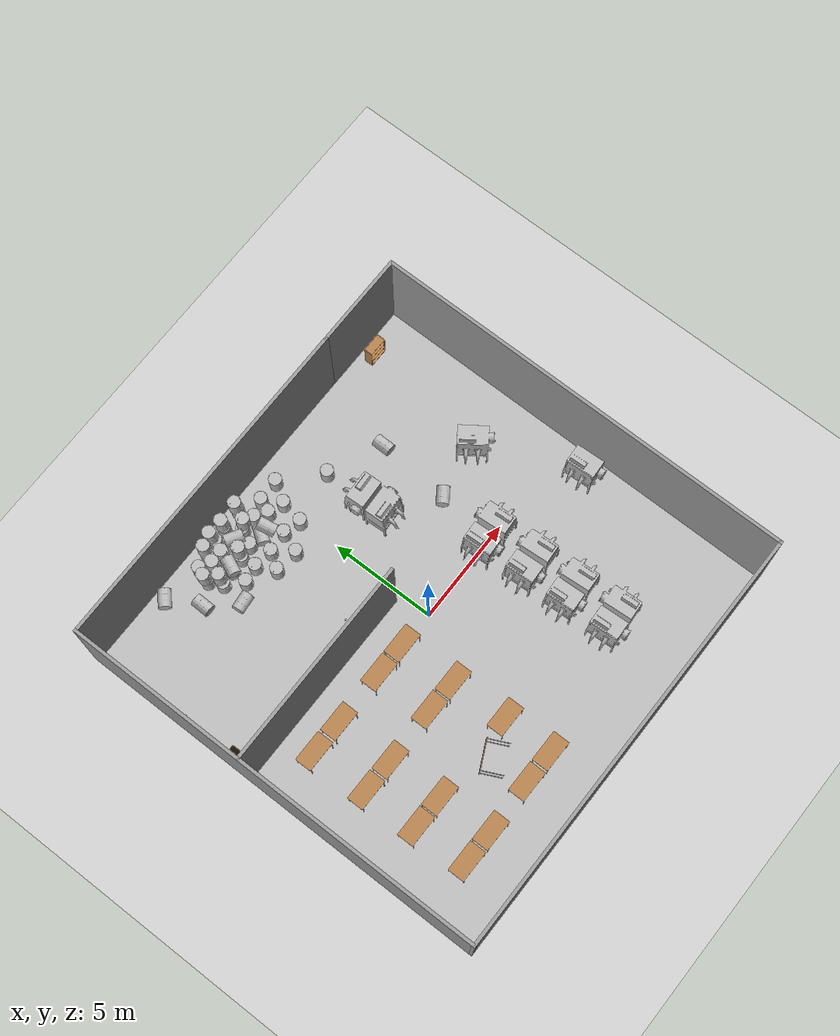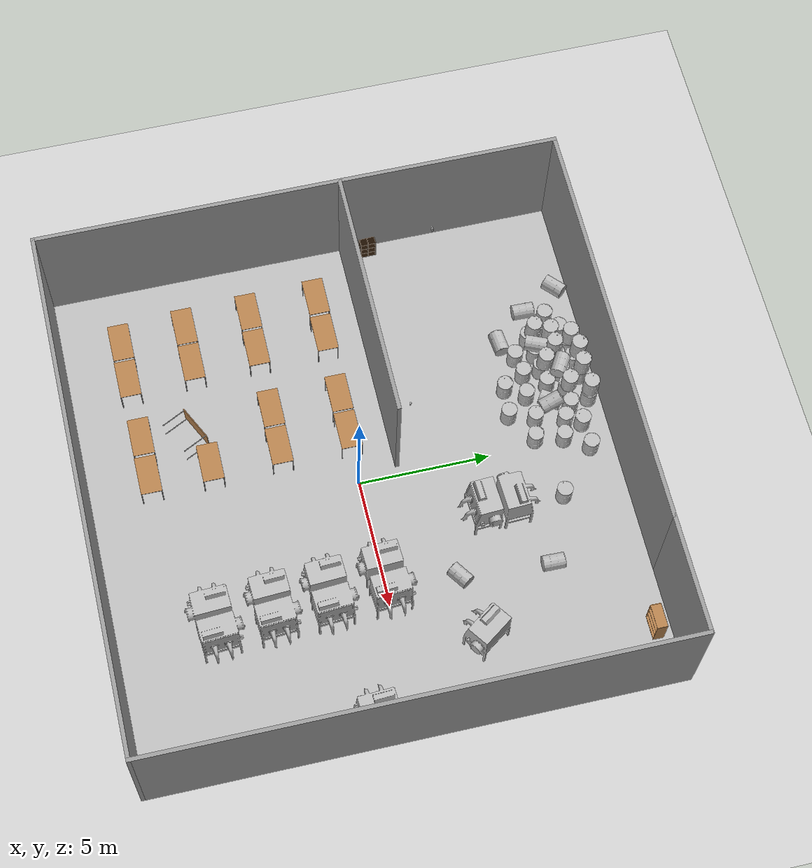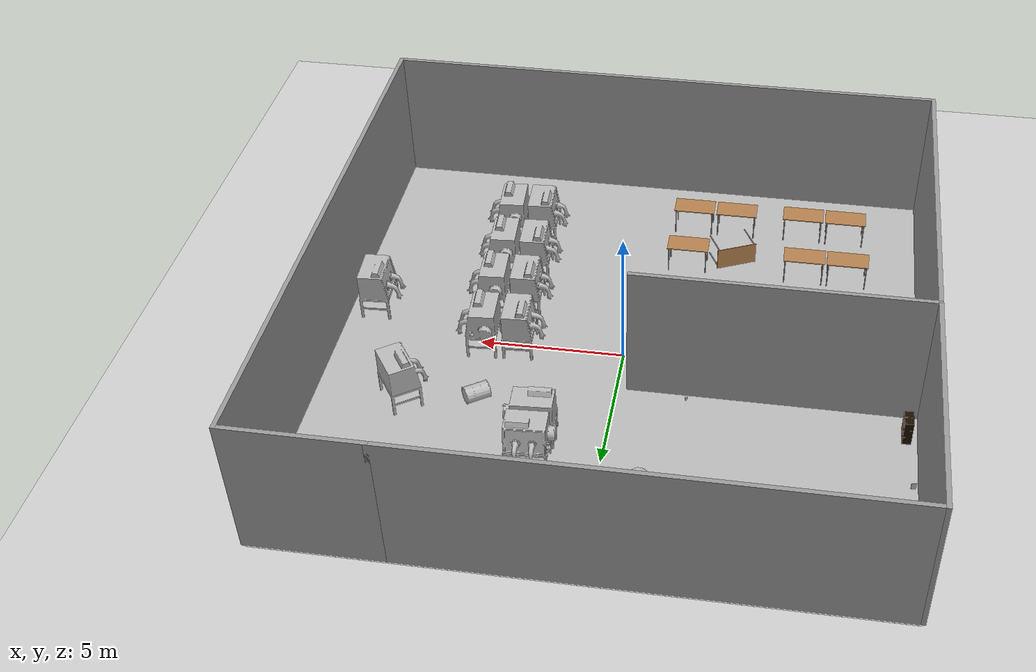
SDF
<sdf version="1.7">
 <world name="default">
  <model name="ground_plane">
   <static>1</static>
   <link name="link">
    <collision name="collision">
     <geometry><plane><normal>0 0 1</normal><size>100 100</size></plane></geometry>
     <surface><friction><ode><mu>100</mu><mu2>50</mu2></ode></friction></surface>
    </collision>
    <visual name="visual">
     <cast_shadows>0</cast_shadows>
     <geometry><plane><normal>0 0 1</normal><size>100 100</size></plane></geometry>
     <material>
      <script><uri>file://media/materials/scripts/gazebo.material</uri><name>Gazebo/Grey</name></script>
     </material>
    </visual>
   </link>
  </model>
  <gravity>0 0 -9.8</gravity>
  <magnetic_field>6e-06 2.3e-05 -4.2e-05</magnetic_field>
  <atmosphere type="adiabatic"/>
  <physics type="ode">
   <max_step_size>0.001</max_step_size>
   <real_time_factor>1</real_time_factor>
   <real_time_update_rate>1000</real_time_update_rate>
  </physics>
  <scene><ambient>0.4 0.4 0.4 1</ambient><background>0.7 0.7 0.7 1</background><shadows>1</shadows></scene>
  <audio><device>default</device></audio>
  <spherical_coordinates>
   <surface_model>EARTH_WGS84</surface_model>
   <latitude_deg>0</latitude_deg>
   <longitude_deg>0</longitude_deg>
   <elevation>0</elevation>
   <heading_deg>0</heading_deg>
  </spherical_coordinates>
  <model name="table">
   <static>1</static>
   <link name="link">
    <collision name="surface">
     <pose>0 0 1 0 -0 0</pose>
     <geometry><box><size>1.5 0.8 0.03</size></box></geometry>
     <surface><friction><ode><mu>0.6</mu><mu2>0.6</mu2></ode></friction></surface>
    </collision>
    <visual name="visual1">
     <pose>0 0 1 0 -0 0</pose>
     <geometry><box><size>1.5 0.8 0.03</size></box></geometry>
     <material>
      <script><uri>file://media/materials/scripts/gazebo.material</uri><name>Gazebo/Wood</name></script>
     </material>
    </visual>
    <collision name="front_left_leg">
     <pose>0.68 0.38 0.5 0 -0 0</pose>
     <geometry><cylinder><radius>0.02</radius><length>1</length></cylinder></geometry>
    </collision>
    <visual name="front_left_leg">
     <pose>0.68 0.38 0.5 0 -0 0</pose>
     <geometry><cylinder><radius>0.02</radius><length>1</length></cylinder></geometry>
     <material>
      <script><uri>file://media/materials/scripts/gazebo.material</uri><name>Gazebo/Grey</name></script>
     </material>
    </visual>
    <collision name="front_right_leg">
     <pose>0.68 -0.38 0.5 0 -0 0</pose>
     <geometry><cylinder><radius>0.02</radius><length>1</length></cylinder></geometry>
    </collision>
    <visual name="front_right_leg">
     <pose>0.68 -0.38 0.5 0 -0 0</pose>
     <geometry><cylinder><radius>0.02</radius><length>1</length></cylinder></geometry>
     <material>
      <script><uri>file://media/materials/scripts/gazebo.material</uri><name>Gazebo/Grey</name></script>
     </material>
    </visual>
    <collision name="back_right_leg">
     <pose>-0.68 -0.38 0.5 0 -0 0</pose>
     <geometry><cylinder><radius>0.02</radius><length>1</length></cylinder></geometry>
    </collision>
    <visual name="back_right_leg">
     <pose>-0.68 -0.38 0.5 0 -0 0</pose>
     <geometry><cylinder><radius>0.02</radius><length>1</length></cylinder></geometry>
     <material>
      <script><uri>file://media/materials/scripts/gazebo.material</uri><name>Gazebo/Grey</name></script>
     </material>
    </visual>
    <collision name="back_left_leg">
     <pose>-0.68 0.38 0.5 0 -0 0</pose>
     <geometry><cylinder><radius>0.02</radius><length>1</length></cylinder></geometry>
    </collision>
    <visual name="back_left_leg">
     <pose>-0.68 0.38 0.5 0 -0 0</pose>
     <geometry><cylinder><radius>0.02</radius><length>1</length></cylinder></geometry>
     <material>
      <script><uri>file://media/materials/scripts/gazebo.material</uri><name>Gazebo/Grey</name></script>
     </material>
    </visual>
   </link>
   <pose>-7.55177 -2.65765 0 0 -0 0</pose>
  </model>
  <model name="table_clone">
   <static>1</static>
   <link name="link">
    <collision name="surface">
     <pose>0 0 1 0 -0 0</pose>
     <geometry><box><size>1.5 0.8 0.03</size></box></geometry>
     <surface><friction><ode><mu>0.6</mu><mu2>0.6</mu2></ode></friction></surface>
    </collision>
    <visual name="visual1">
     <pose>0 0 1 0 -0 0</pose>
     <geometry><box><size>1.5 0.8 0.03</size></box></geometry>
     <material>
      <script><uri>file://media/materials/scripts/gazebo.material</uri><name>Gazebo/Wood</name></script>
     </material>
    </visual>
    <collision name="front_left_leg">
     <pose>0.68 0.38 0.5 0 -0 0</pose>
     <geometry><cylinder><radius>0.02</radius><length>1</length></cylinder></geometry>
    </collision>
    <visual name="front_left_leg">
     <pose>0.68 0.38 0.5 0 -0 0</pose>
     <geometry><cylinder><radius>0.02</radius><length>1</length></cylinder></geometry>
     <material>
      <script><uri>file://media/materials/scripts/gazebo.material</uri><name>Gazebo/Grey</name></script>
     </material>
    </visual>
    <collision name="front_right_leg">
     <pose>0.68 -0.38 0.5 0 -0 0</pose>
     <geometry><cylinder><radius>0.02</radius><length>1</length></cylinder></geometry>
    </collision>
    <visual name="front_right_leg">
     <pose>0.68 -0.38 0.5 0 -0 0</pose>
     <geometry><cylinder><radius>0.02</radius><length>1</length></cylinder></geometry>
     <material>
      <script><uri>file://media/materials/scripts/gazebo.material</uri><name>Gazebo/Grey</name></script>
     </material>
    </visual>
    <collision name="back_right_leg">
     <pose>-0.68 -0.38 0.5 0 -0 0</pose>
     <geometry><cylinder><radius>0.02</radius><length>1</length></cylinder></geometry>
    </collision>
    <visual name="back_right_leg">
     <pose>-0.68 -0.38 0.5 0 -0 0</pose>
     <geometry><cylinder><radius>0.02</radius><length>1</length></cylinder></geometry>
     <material>
      <script><uri>file://media/materials/scripts/gazebo.material</uri><name>Gazebo/Grey</name></script>
     </material>
    </visual>
    <collision name="back_left_leg">
     <pose>-0.68 0.38 0.5 0 -0 0</pose>
     <geometry><cylinder><radius>0.02</radius><length>1</length></cylinder></geometry>
    </collision>
    <visual name="back_left_leg">
     <pose>-0.68 0.38 0.5 0 -0 0</pose>
     <geometry><cylinder><radius>0.02</radius><length>1</length></cylinder></geometry>
     <material>
      <script><uri>file://media/materials/scripts/gazebo.material</uri><name>Gazebo/Grey</name></script>
     </material>
    </visual>
   </link>
   <pose>-5.96904 -2.67059 0 0 -0 0</pose>
  </model>
  <model name="table_clone_0">
   <static>1</static>
   <link name="link">
    <collision name="surface">
     <pose>0 0 1 0 -0 0</pose>
     <geometry><box><size>1.5 0.8 0.03</size></box></geometry>
     <surface><friction><ode><mu>0.6</mu><mu2>0.6</mu2></ode></friction></surface>
    </collision>
    <visual name="visual1">
     <pose>0 0 1 0 -0 0</pose>
     <geometry><box><size>1.5 0.8 0.03</size></box></geometry>
     <material>
      <script><uri>file://media/materials/scripts/gazebo.material</uri><name>Gazebo/Wood</name></script>
     </material>
    </visual>
    <collision name="front_left_leg">
     <pose>0.68 0.38 0.5 0 -0 0</pose>
     <geometry><cylinder><radius>0.02</radius><length>1</length></cylinder></geometry>
    </collision>
    <visual name="front_left_leg">
     <pose>0.68 0.38 0.5 0 -0 0</pose>
     <geometry><cylinder><radius>0.02</radius><length>1</length></cylinder></geometry>
     <material>
      <script><uri>file://media/materials/scripts/gazebo.material</uri><name>Gazebo/Grey</name></script>
     </material>
    </visual>
    <collision name="front_right_leg">
     <pose>0.68 -0.38 0.5 0 -0 0</pose>
     <geometry><cylinder><radius>0.02</radius><length>1</length></cylinder></geometry>
    </collision>
    <visual name="front_right_leg">
     <pose>0.68 -0.38 0.5 0 -0 0</pose>
     <geometry><cylinder><radius>0.02</radius><length>1</length></cylinder></geometry>
     <material>
      <script><uri>file://media/materials/scripts/gazebo.material</uri><name>Gazebo/Grey</name></script>
     </material>
    </visual>
    <collision name="back_right_leg">
     <pose>-0.68 -0.38 0.5 0 -0 0</pose>
     <geometry><cylinder><radius>0.02</radius><length>1</length></cylinder></geometry>
    </collision>
    <visual name="back_right_leg">
     <pose>-0.68 -0.38 0.5 0 -0 0</pose>
     <geometry><cylinder><radius>0.02</radius><length>1</length></cylinder></geometry>
     <material>
      <script><uri>file://media/materials/scripts/gazebo.material</uri><name>Gazebo/Grey</name></script>
     </material>
    </visual>
    <collision name="back_left_leg">
     <pose>-0.68 0.38 0.5 0 -0 0</pose>
     <geometry><cylinder><radius>0.02</radius><length>1</length></cylinder></geometry>
    </collision>
    <visual name="back_left_leg">
     <pose>-0.68 0.38 0.5 0 -0 0</pose>
     <geometry><cylinder><radius>0.02</radius><length>1</length></cylinder></geometry>
     <material>
      <script><uri>file://media/materials/scripts/gazebo.material</uri><name>Gazebo/Grey</name></script>
     </material>
    </visual>
   </link>
   <pose>-3.33754 -2.64504 0 0 -0 0</pose>
  </model>
  <model name="table_clone_1">
   <static>1</static>
   <link name="link">
    <collision name="surface">
     <pose>0 0 1 0 -0 0</pose>
     <geometry><box><size>1.5 0.8 0.03</size></box></geometry>
     <surface><friction><ode><mu>0.6</mu><mu2>0.6</mu2></ode></friction></surface>
    </collision>
    <visual name="visual1">
     <pose>0 0 1 0 -0 0</pose>
     <geometry><box><size>1.5 0.8 0.03</size></box></geometry>
     <material>
      <script><uri>file://media/materials/scripts/gazebo.material</uri><name>Gazebo/Wood</name></script>
     </material>
    </visual>
    <collision name="front_left_leg">
     <pose>0.68 0.38 0.5 0 -0 0</pose>
     <geometry><cylinder><radius>0.02</radius><length>1</length></cylinder></geometry>
    </collision>
    <visual name="front_left_leg">
     <pose>0.68 0.38 0.5 0 -0 0</pose>
     <geometry><cylinder><radius>0.02</radius><length>1</length></cylinder></geometry>
     <material>
      <script><uri>file://media/materials/scripts/gazebo.material</uri><name>Gazebo/Grey</name></script>
     </material>
    </visual>
    <collision name="front_right_leg">
     <pose>0.68 -0.38 0.5 0 -0 0</pose>
     <geometry><cylinder><radius>0.02</radius><length>1</length></cylinder></geometry>
    </collision>
    <visual name="front_right_leg">
     <pose>0.68 -0.38 0.5 0 -0 0</pose>
     <geometry><cylinder><radius>0.02</radius><length>1</length></cylinder></geometry>
     <material>
      <script><uri>file://media/materials/scripts/gazebo.material</uri><name>Gazebo/Grey</name></script>
     </material>
    </visual>
    <collision name="back_right_leg">
     <pose>-0.68 -0.38 0.5 0 -0 0</pose>
     <geometry><cylinder><radius>0.02</radius><length>1</length></cylinder></geometry>
    </collision>
    <visual name="back_right_leg">
     <pose>-0.68 -0.38 0.5 0 -0 0</pose>
     <geometry><cylinder><radius>0.02</radius><length>1</length></cylinder></geometry>
     <material>
      <script><uri>file://media/materials/scripts/gazebo.material</uri><name>Gazebo/Grey</name></script>
     </material>
    </visual>
    <collision name="back_left_leg">
     <pose>-0.68 0.38 0.5 0 -0 0</pose>
     <geometry><cylinder><radius>0.02</radius><length>1</length></cylinder></geometry>
    </collision>
    <visual name="back_left_leg">
     <pose>-0.68 0.38 0.5 0 -0 0</pose>
     <geometry><cylinder><radius>0.02</radius><length>1</length></cylinder></geometry>
     <material>
      <script><uri>file://media/materials/scripts/gazebo.material</uri><name>Gazebo/Grey</name></script>
     </material>
    </visual>
   </link>
   <pose>-1.76077 -2.66222 0 0 -0 0</pose>
  </model>
  <model name="table_clone_2">
   <static>1</static>
   <link name="link">
    <collision name="surface">
     <pose>0 0 1 0 -0 0</pose>
     <geometry><box><size>1.5 0.8 0.03</size></box></geometry>
     <surface><friction><ode><mu>0.6</mu><mu2>0.6</mu2></ode></friction></surface>
    </collision>
    <visual name="visual1">
     <pose>0 0 1 0 -0 0</pose>
     <geometry><box><size>1.5 0.8 0.03</size></box></geometry>
     <material>
      <script><uri>file://media/materials/scripts/gazebo.material</uri><name>Gazebo/Wood</name></script>
     </material>
    </visual>
    <collision name="front_left_leg">
     <pose>0.68 0.38 0.5 0 -0 0</pose>
     <geometry><cylinder><radius>0.02</radius><length>1</length></cylinder></geometry>
    </collision>
    <visual name="front_left_leg">
     <pose>0.68 0.38 0.5 0 -0 0</pose>
     <geometry><cylinder><radius>0.02</radius><length>1</length></cylinder></geometry>
     <material>
      <script><uri>file://media/materials/scripts/gazebo.material</uri><name>Gazebo/Grey</name></script>
     </material>
    </visual>
    <collision name="front_right_leg">
     <pose>0.68 -0.38 0.5 0 -0 0</pose>
     <geometry><cylinder><radius>0.02</radius><length>1</length></cylinder></geometry>
    </collision>
    <visual name="front_right_leg">
     <pose>0.68 -0.38 0.5 0 -0 0</pose>
     <geometry><cylinder><radius>0.02</radius><length>1</length></cylinder></geometry>
     <material>
      <script><uri>file://media/materials/scripts/gazebo.material</uri><name>Gazebo/Grey</name></script>
     </material>
    </visual>
    <collision name="back_right_leg">
     <pose>-0.68 -0.38 0.5 0 -0 0</pose>
     <geometry><cylinder><radius>0.02</radius><length>1</length></cylinder></geometry>
    </collision>
    <visual name="back_right_leg">
     <pose>-0.68 -0.38 0.5 0 -0 0</pose>
     <geometry><cylinder><radius>0.02</radius><length>1</length></cylinder></geometry>
     <material>
      <script><uri>file://media/materials/scripts/gazebo.material</uri><name>Gazebo/Grey</name></script>
     </material>
    </visual>
    <collision name="back_left_leg">
     <pose>-0.68 0.38 0.5 0 -0 0</pose>
     <geometry><cylinder><radius>0.02</radius><length>1</length></cylinder></geometry>
    </collision>
    <visual name="back_left_leg">
     <pose>-0.68 0.38 0.5 0 -0 0</pose>
     <geometry><cylinder><radius>0.02</radius><length>1</length></cylinder></geometry>
     <material>
      <script><uri>file://media/materials/scripts/gazebo.material</uri><name>Gazebo/Grey</name></script>
     </material>
    </visual>
   </link>
   <pose>-7.46217 -5.18144 0 0 -0 0</pose>
  </model>
  <model name="table_clone_3">
   <static>1</static>
   <link name="link">
    <collision name="surface">
     <pose>0 0 1 0 -0 0</pose>
     <geometry><box><size>1.5 0.8 0.03</size></box></geometry>
     <surface><friction><ode><mu>0.6</mu><mu2>0.6</mu2></ode></friction></surface>
    </collision>
    <visual name="visual1">
     <pose>0 0 1 0 -0 0</pose>
     <geometry><box><size>1.5 0.8 0.03</size></box></geometry>
     <material>
      <script><uri>file://media/materials/scripts/gazebo.material</uri><name>Gazebo/Wood</name></script>
     </material>
    </visual>
    <collision name="front_left_leg">
     <pose>0.68 0.38 0.5 0 -0 0</pose>
     <geometry><cylinder><radius>0.02</radius><length>1</length></cylinder></geometry>
    </collision>
    <visual name="front_left_leg">
     <pose>0.68 0.38 0.5 0 -0 0</pose>
     <geometry><cylinder><radius>0.02</radius><length>1</length></cylinder></geometry>
     <material>
      <script><uri>file://media/materials/scripts/gazebo.material</uri><name>Gazebo/Grey</name></script>
     </material>
    </visual>
    <collision name="front_right_leg">
     <pose>0.68 -0.38 0.5 0 -0 0</pose>
     <geometry><cylinder><radius>0.02</radius><length>1</length></cylinder></geometry>
    </collision>
    <visual name="front_right_leg">
     <pose>0.68 -0.38 0.5 0 -0 0</pose>
     <geometry><cylinder><radius>0.02</radius><length>1</length></cylinder></geometry>
     <material>
      <script><uri>file://media/materials/scripts/gazebo.material</uri><name>Gazebo/Grey</name></script>
     </material>
    </visual>
    <collision name="back_right_leg">
     <pose>-0.68 -0.38 0.5 0 -0 0</pose>
     <geometry><cylinder><radius>0.02</radius><length>1</length></cylinder></geometry>
    </collision>
    <visual name="back_right_leg">
     <pose>-0.68 -0.38 0.5 0 -0 0</pose>
     <geometry><cylinder><radius>0.02</radius><length>1</length></cylinder></geometry>
     <material>
      <script><uri>file://media/materials/scripts/gazebo.material</uri><name>Gazebo/Grey</name></script>
     </material>
    </visual>
    <collision name="back_left_leg">
     <pose>-0.68 0.38 0.5 0 -0 0</pose>
     <geometry><cylinder><radius>0.02</radius><length>1</length></cylinder></geometry>
    </collision>
    <visual name="back_left_leg">
     <pose>-0.68 0.38 0.5 0 -0 0</pose>
     <geometry><cylinder><radius>0.02</radius><length>1</length></cylinder></geometry>
     <material>
      <script><uri>file://media/materials/scripts/gazebo.material</uri><name>Gazebo/Grey</name></script>
     </material>
    </visual>
   </link>
   <pose>-5.90194 -5.18683 0 0 -0 0</pose>
  </model>
  <model name="table_clone_5">
   <static>1</static>
   <link name="link">
    <collision name="surface">
     <pose>0 0 1 0 -0 0</pose>
     <geometry><box><size>1.5 0.8 0.03</size></box></geometry>
     <surface><friction><ode><mu>0.6</mu><mu2>0.6</mu2></ode></friction></surface>
    </collision>
    <visual name="visual1">
     <pose>0 0 1 0 -0 0</pose>
     <geometry><box><size>1.5 0.8 0.03</size></box></geometry>
     <material>
      <script><uri>file://media/materials/scripts/gazebo.material</uri><name>Gazebo/Wood</name></script>
     </material>
    </visual>
    <collision name="front_left_leg">
     <pose>0.68 0.38 0.5 0 -0 0</pose>
     <geometry><cylinder><radius>0.02</radius><length>1</length></cylinder></geometry>
    </collision>
    <visual name="front_left_leg">
     <pose>0.68 0.38 0.5 0 -0 0</pose>
     <geometry><cylinder><radius>0.02</radius><length>1</length></cylinder></geometry>
     <material>
      <script><uri>file://media/materials/scripts/gazebo.material</uri><name>Gazebo/Grey</name></script>
     </material>
    </visual>
    <collision name="front_right_leg">
     <pose>0.68 -0.38 0.5 0 -0 0</pose>
     <geometry><cylinder><radius>0.02</radius><length>1</length></cylinder></geometry>
    </collision>
    <visual name="front_right_leg">
     <pose>0.68 -0.38 0.5 0 -0 0</pose>
     <geometry><cylinder><radius>0.02</radius><length>1</length></cylinder></geometry>
     <material>
      <script><uri>file://media/materials/scripts/gazebo.material</uri><name>Gazebo/Grey</name></script>
     </material>
    </visual>
    <collision name="back_right_leg">
     <pose>-0.68 -0.38 0.5 0 -0 0</pose>
     <geometry><cylinder><radius>0.02</radius><length>1</length></cylinder></geometry>
    </collision>
    <visual name="back_right_leg">
     <pose>-0.68 -0.38 0.5 0 -0 0</pose>
     <geometry><cylinder><radius>0.02</radius><length>1</length></cylinder></geometry>
     <material>
      <script><uri>file://media/materials/scripts/gazebo.material</uri><name>Gazebo/Grey</name></script>
     </material>
    </visual>
    <collision name="back_left_leg">
     <pose>-0.68 0.38 0.5 0 -0 0</pose>
     <geometry><cylinder><radius>0.02</radius><length>1</length></cylinder></geometry>
    </collision>
    <visual name="back_left_leg">
     <pose>-0.68 0.38 0.5 0 -0 0</pose>
     <geometry><cylinder><radius>0.02</radius><length>1</length></cylinder></geometry>
     <material>
      <script><uri>file://media/materials/scripts/gazebo.material</uri><name>Gazebo/Grey</name></script>
     </material>
    </visual>
   </link>
   <pose>-1.65 -5.29392 0 0 -0 0</pose>
  </model>
  <model name="table_clone_6">
   <static>1</static>
   <link name="link">
    <collision name="surface">
     <pose>0 0 1 0 -0 0</pose>
     <geometry><box><size>1.5 0.8 0.03</size></box></geometry>
     <surface><friction><ode><mu>0.6</mu><mu2>0.6</mu2></ode></friction></surface>
    </collision>
    <visual name="visual1">
     <pose>0 0 1 0 -0 0</pose>
     <geometry><box><size>1.5 0.8 0.03</size></box></geometry>
     <material>
      <script><uri>file://media/materials/scripts/gazebo.material</uri><name>Gazebo/Wood</name></script>
     </material>
    </visual>
    <collision name="front_left_leg">
     <pose>0.68 0.38 0.5 0 -0 0</pose>
     <geometry><cylinder><radius>0.02</radius><length>1</length></cylinder></geometry>
    </collision>
    <visual name="front_left_leg">
     <pose>0.68 0.38 0.5 0 -0 0</pose>
     <geometry><cylinder><radius>0.02</radius><length>1</length></cylinder></geometry>
     <material>
      <script><uri>file://media/materials/scripts/gazebo.material</uri><name>Gazebo/Grey</name></script>
     </material>
    </visual>
    <collision name="front_right_leg">
     <pose>0.68 -0.38 0.5 0 -0 0</pose>
     <geometry><cylinder><radius>0.02</radius><length>1</length></cylinder></geometry>
    </collision>
    <visual name="front_right_leg">
     <pose>0.68 -0.38 0.5 0 -0 0</pose>
     <geometry><cylinder><radius>0.02</radius><length>1</length></cylinder></geometry>
     <material>
      <script><uri>file://media/materials/scripts/gazebo.material</uri><name>Gazebo/Grey</name></script>
     </material>
    </visual>
    <collision name="back_right_leg">
     <pose>-0.68 -0.38 0.5 0 -0 0</pose>
     <geometry><cylinder><radius>0.02</radius><length>1</length></cylinder></geometry>
    </collision>
    <visual name="back_right_leg">
     <pose>-0.68 -0.38 0.5 0 -0 0</pose>
     <geometry><cylinder><radius>0.02</radius><length>1</length></cylinder></geometry>
     <material>
      <script><uri>file://media/materials/scripts/gazebo.material</uri><name>Gazebo/Grey</name></script>
     </material>
    </visual>
    <collision name="back_left_leg">
     <pose>-0.68 0.38 0.5 0 -0 0</pose>
     <geometry><cylinder><radius>0.02</radius><length>1</length></cylinder></geometry>
    </collision>
    <visual name="back_left_leg">
     <pose>-0.68 0.38 0.5 0 -0 0</pose>
     <geometry><cylinder><radius>0.02</radius><length>1</length></cylinder></geometry>
     <material>
      <script><uri>file://media/materials/scripts/gazebo.material</uri><name>Gazebo/Grey</name></script>
     </material>
    </visual>
   </link>
   <pose>-7.31794 -7.66718 0 0 -0 0</pose>
  </model>
  <model name="table_clone_7">
   <static>1</static>
   <link name="link">
    <collision name="surface">
     <pose>0 0 1 0 -0 0</pose>
     <geometry><box><size>1.5 0.8 0.03</size></box></geometry>
     <surface><friction><ode><mu>0.6</mu><mu2>0.6</mu2></ode></friction></surface>
    </collision>
    <visual name="visual1">
     <pose>0 0 1 0 -0 0</pose>
     <geometry><box><size>1.5 0.8 0.03</size></box></geometry>
     <material>
      <script><uri>file://media/materials/scripts/gazebo.material</uri><name>Gazebo/Wood</name></script>
     </material>
    </visual>
    <collision name="front_left_leg">
     <pose>0.68 0.38 0.5 0 -0 0</pose>
     <geometry><cylinder><radius>0.02</radius><length>1</length></cylinder></geometry>
    </collision>
    <visual name="front_left_leg">
     <pose>0.68 0.38 0.5 0 -0 0</pose>
     <geometry><cylinder><radius>0.02</radius><length>1</length></cylinder></geometry>
     <material>
      <script><uri>file://media/materials/scripts/gazebo.material</uri><name>Gazebo/Grey</name></script>
     </material>
    </visual>
    <collision name="front_right_leg">
     <pose>0.68 -0.38 0.5 0 -0 0</pose>
     <geometry><cylinder><radius>0.02</radius><length>1</length></cylinder></geometry>
    </collision>
    <visual name="front_right_leg">
     <pose>0.68 -0.38 0.5 0 -0 0</pose>
     <geometry><cylinder><radius>0.02</radius><length>1</length></cylinder></geometry>
     <material>
      <script><uri>file://media/materials/scripts/gazebo.material</uri><name>Gazebo/Grey</name></script>
     </material>
    </visual>
    <collision name="back_right_leg">
     <pose>-0.68 -0.38 0.5 0 -0 0</pose>
     <geometry><cylinder><radius>0.02</radius><length>1</length></cylinder></geometry>
    </collision>
    <visual name="back_right_leg">
     <pose>-0.68 -0.38 0.5 0 -0 0</pose>
     <geometry><cylinder><radius>0.02</radius><length>1</length></cylinder></geometry>
     <material>
      <script><uri>file://media/materials/scripts/gazebo.material</uri><name>Gazebo/Grey</name></script>
     </material>
    </visual>
    <collision name="back_left_leg">
     <pose>-0.68 0.38 0.5 0 -0 0</pose>
     <geometry><cylinder><radius>0.02</radius><length>1</length></cylinder></geometry>
    </collision>
    <visual name="back_left_leg">
     <pose>-0.68 0.38 0.5 0 -0 0</pose>
     <geometry><cylinder><radius>0.02</radius><length>1</length></cylinder></geometry>
     <material>
      <script><uri>file://media/materials/scripts/gazebo.material</uri><name>Gazebo/Grey</name></script>
     </material>
    </visual>
   </link>
   <pose>-5.73834 -7.67638 0 0 -0 0</pose>
  </model>
  <model name="table_clone_8">
   <static>1</static>
   <link name="link">
    <collision name="surface">
     <pose>0 0 1 0 -0 0</pose>
     <geometry><box><size>1.5 0.8 0.03</size></box></geometry>
     <surface><friction><ode><mu>0.6</mu><mu2>0.6</mu2></ode></friction></surface>
    </collision>
    <visual name="visual1">
     <pose>0 0 1 0 -0 0</pose>
     <geometry><box><size>1.5 0.8 0.03</size></box></geometry>
     <material>
      <script><uri>file://media/materials/scripts/gazebo.material</uri><name>Gazebo/Wood</name></script>
     </material>
    </visual>
    <collision name="front_left_leg">
     <pose>0.68 0.38 0.5 0 -0 0</pose>
     <geometry><cylinder><radius>0.02</radius><length>1</length></cylinder></geometry>
    </collision>
    <visual name="front_left_leg">
     <pose>0.68 0.38 0.5 0 -0 0</pose>
     <geometry><cylinder><radius>0.02</radius><length>1</length></cylinder></geometry>
     <material>
      <script><uri>file://media/materials/scripts/gazebo.material</uri><name>Gazebo/Grey</name></script>
     </material>
    </visual>
    <collision name="front_right_leg">
     <pose>0.68 -0.38 0.5 0 -0 0</pose>
     <geometry><cylinder><radius>0.02</radius><length>1</length></cylinder></geometry>
    </collision>
    <visual name="front_right_leg">
     <pose>0.68 -0.38 0.5 0 -0 0</pose>
     <geometry><cylinder><radius>0.02</radius><length>1</length></cylinder></geometry>
     <material>
      <script><uri>file://media/materials/scripts/gazebo.material</uri><name>Gazebo/Grey</name></script>
     </material>
    </visual>
    <collision name="back_right_leg">
     <pose>-0.68 -0.38 0.5 0 -0 0</pose>
     <geometry><cylinder><radius>0.02</radius><length>1</length></cylinder></geometry>
    </collision>
    <visual name="back_right_leg">
     <pose>-0.68 -0.38 0.5 0 -0 0</pose>
     <geometry><cylinder><radius>0.02</radius><length>1</length></cylinder></geometry>
     <material>
      <script><uri>file://media/materials/scripts/gazebo.material</uri><name>Gazebo/Grey</name></script>
     </material>
    </visual>
    <collision name="back_left_leg">
     <pose>-0.68 0.38 0.5 0 -0 0</pose>
     <geometry><cylinder><radius>0.02</radius><length>1</length></cylinder></geometry>
    </collision>
    <visual name="back_left_leg">
     <pose>-0.68 0.38 0.5 0 -0 0</pose>
     <geometry><cylinder><radius>0.02</radius><length>1</length></cylinder></geometry>
     <material>
      <script><uri>file://media/materials/scripts/gazebo.material</uri><name>Gazebo/Grey</name></script>
     </material>
    </visual>
   </link>
   <pose>-3.24202 -7.62181 0 0 -0 0</pose>
  </model>
  <model name="table_clone_9">
   <static>1</static>
   <link name="link">
    <collision name="surface">
     <pose>0 0 1 0 -0 0</pose>
     <geometry><box><size>1.5 0.8 0.03</size></box></geometry>
     <surface><friction><ode><mu>0.6</mu><mu2>0.6</mu2></ode></friction></surface>
    </collision>
    <visual name="visual1">
     <pose>0 0 1 0 -0 0</pose>
     <geometry><box><size>1.5 0.8 0.03</size></box></geometry>
     <material>
      <script><uri>file://media/materials/scripts/gazebo.material</uri><name>Gazebo/Wood</name></script>
     </material>
    </visual>
    <collision name="front_left_leg">
     <pose>0.68 0.38 0.5 0 -0 0</pose>
     <geometry><cylinder><radius>0.02</radius><length>1</length></cylinder></geometry>
    </collision>
    <visual name="front_left_leg">
     <pose>0.68 0.38 0.5 0 -0 0</pose>
     <geometry><cylinder><radius>0.02</radius><length>1</length></cylinder></geometry>
     <material>
      <script><uri>file://media/materials/scripts/gazebo.material</uri><name>Gazebo/Grey</name></script>
     </material>
    </visual>
    <collision name="front_right_leg">
     <pose>0.68 -0.38 0.5 0 -0 0</pose>
     <geometry><cylinder><radius>0.02</radius><length>1</length></cylinder></geometry>
    </collision>
    <visual name="front_right_leg">
     <pose>0.68 -0.38 0.5 0 -0 0</pose>
     <geometry><cylinder><radius>0.02</radius><length>1</length></cylinder></geometry>
     <material>
      <script><uri>file://media/materials/scripts/gazebo.material</uri><name>Gazebo/Grey</name></script>
     </material>
    </visual>
    <collision name="back_right_leg">
     <pose>-0.68 -0.38 0.5 0 -0 0</pose>
     <geometry><cylinder><radius>0.02</radius><length>1</length></cylinder></geometry>
    </collision>
    <visual name="back_right_leg">
     <pose>-0.68 -0.38 0.5 0 -0 0</pose>
     <geometry><cylinder><radius>0.02</radius><length>1</length></cylinder></geometry>
     <material>
      <script><uri>file://media/materials/scripts/gazebo.material</uri><name>Gazebo/Grey</name></script>
     </material>
    </visual>
    <collision name="back_left_leg">
     <pose>-0.68 0.38 0.5 0 -0 0</pose>
     <geometry><cylinder><radius>0.02</radius><length>1</length></cylinder></geometry>
    </collision>
    <visual name="back_left_leg">
     <pose>-0.68 0.38 0.5 0 -0 0</pose>
     <geometry><cylinder><radius>0.02</radius><length>1</length></cylinder></geometry>
     <material>
      <script><uri>file://media/materials/scripts/gazebo.material</uri><name>Gazebo/Grey</name></script>
     </material>
    </visual>
   </link>
   <pose>-1.64837 -7.6314 0 0 -0 0</pose>
  </model>
  <model name="table_clone_10">
   <static>1</static>
   <link name="link">
    <collision name="surface">
     <pose>0 0 1 0 -0 0</pose>
     <geometry><box><size>1.5 0.8 0.03</size></box></geometry>
     <surface><friction><ode><mu>0.6</mu><mu2>0.6</mu2></ode></friction></surface>
    </collision>
    <visual name="visual1">
     <pose>0 0 1 0 -0 0</pose>
     <geometry><box><size>1.5 0.8 0.03</size></box></geometry>
     <material>
      <script><uri>file://media/materials/scripts/gazebo.material</uri><name>Gazebo/Wood</name></script>
     </material>
    </visual>
    <collision name="front_left_leg">
     <pose>0.68 0.38 0.5 0 -0 0</pose>
     <geometry><cylinder><radius>0.02</radius><length>1</length></cylinder></geometry>
    </collision>
    <visual name="front_left_leg">
     <pose>0.68 0.38 0.5 0 -0 0</pose>
     <geometry><cylinder><radius>0.02</radius><length>1</length></cylinder></geometry>
     <material>
      <script><uri>file://media/materials/scripts/gazebo.material</uri><name>Gazebo/Grey</name></script>
     </material>
    </visual>
    <collision name="front_right_leg">
     <pose>0.68 -0.38 0.5 0 -0 0</pose>
     <geometry><cylinder><radius>0.02</radius><length>1</length></cylinder></geometry>
    </collision>
    <visual name="front_right_leg">
     <pose>0.68 -0.38 0.5 0 -0 0</pose>
     <geometry><cylinder><radius>0.02</radius><length>1</length></cylinder></geometry>
     <material>
      <script><uri>file://media/materials/scripts/gazebo.material</uri><name>Gazebo/Grey</name></script>
     </material>
    </visual>
    <collision name="back_right_leg">
     <pose>-0.68 -0.38 0.5 0 -0 0</pose>
     <geometry><cylinder><radius>0.02</radius><length>1</length></cylinder></geometry>
    </collision>
    <visual name="back_right_leg">
     <pose>-0.68 -0.38 0.5 0 -0 0</pose>
     <geometry><cylinder><radius>0.02</radius><length>1</length></cylinder></geometry>
     <material>
      <script><uri>file://media/materials/scripts/gazebo.material</uri><name>Gazebo/Grey</name></script>
     </material>
    </visual>
    <collision name="back_left_leg">
     <pose>-0.68 0.38 0.5 0 -0 0</pose>
     <geometry><cylinder><radius>0.02</radius><length>1</length></cylinder></geometry>
    </collision>
    <visual name="back_left_leg">
     <pose>-0.68 0.38 0.5 0 -0 0</pose>
     <geometry><cylinder><radius>0.02</radius><length>1</length></cylinder></geometry>
     <material>
      <script><uri>file://media/materials/scripts/gazebo.material</uri><name>Gazebo/Grey</name></script>
     </material>
    </visual>
   </link>
   <pose>-7.61701 0.015326 0 0 -0 0</pose>
  </model>
  <model name="table_clone_11">
   <static>1</static>
   <link name="link">
    <collision name="surface">
     <pose>0 0 1 0 -0 0</pose>
     <geometry><box><size>1.5 0.8 0.03</size></box></geometry>
     <surface><friction><ode><mu>0.6</mu><mu2>0.6</mu2></ode></friction></surface>
    </collision>
    <visual name="visual1">
     <pose>0 0 1 0 -0 0</pose>
     <geometry><box><size>1.5 0.8 0.03</size></box></geometry>
     <material>
      <script><uri>file://media/materials/scripts/gazebo.material</uri><name>Gazebo/Wood</name></script>
     </material>
    </visual>
    <collision name="front_left_leg">
     <pose>0.68 0.38 0.5 0 -0 0</pose>
     <geometry><cylinder><radius>0.02</radius><length>1</length></cylinder></geometry>
    </collision>
    <visual name="front_left_leg">
     <pose>0.68 0.38 0.5 0 -0 0</pose>
     <geometry><cylinder><radius>0.02</radius><length>1</length></cylinder></geometry>
     <material>
      <script><uri>file://media/materials/scripts/gazebo.material</uri><name>Gazebo/Grey</name></script>
     </material>
    </visual>
    <collision name="front_right_leg">
     <pose>0.68 -0.38 0.5 0 -0 0</pose>
     <geometry><cylinder><radius>0.02</radius><length>1</length></cylinder></geometry>
    </collision>
    <visual name="front_right_leg">
     <pose>0.68 -0.38 0.5 0 -0 0</pose>
     <geometry><cylinder><radius>0.02</radius><length>1</length></cylinder></geometry>
     <material>
      <script><uri>file://media/materials/scripts/gazebo.material</uri><name>Gazebo/Grey</name></script>
     </material>
    </visual>
    <collision name="back_right_leg">
     <pose>-0.68 -0.38 0.5 0 -0 0</pose>
     <geometry><cylinder><radius>0.02</radius><length>1</length></cylinder></geometry>
    </collision>
    <visual name="back_right_leg">
     <pose>-0.68 -0.38 0.5 0 -0 0</pose>
     <geometry><cylinder><radius>0.02</radius><length>1</length></cylinder></geometry>
     <material>
      <script><uri>file://media/materials/scripts/gazebo.material</uri><name>Gazebo/Grey</name></script>
     </material>
    </visual>
    <collision name="back_left_leg">
     <pose>-0.68 0.38 0.5 0 -0 0</pose>
     <geometry><cylinder><radius>0.02</radius><length>1</length></cylinder></geometry>
    </collision>
    <visual name="back_left_leg">
     <pose>-0.68 0.38 0.5 0 -0 0</pose>
     <geometry><cylinder><radius>0.02</radius><length>1</length></cylinder></geometry>
     <material>
      <script><uri>file://media/materials/scripts/gazebo.material</uri><name>Gazebo/Grey</name></script>
     </material>
    </visual>
   </link>
   <pose>-6.01438 -0.004729 0 0 -0 0</pose>
  </model>
  <model name="table_clone_12">
   <static>1</static>
   <link name="link">
    <collision name="surface">
     <pose>0 0 1 0 -0 0</pose>
     <geometry><box><size>1.5 0.8 0.03</size></box></geometry>
     <surface><friction><ode><mu>0.6</mu><mu2>0.6</mu2></ode></friction></surface>
    </collision>
    <visual name="visual1">
     <pose>0 0 1 0 -0 0</pose>
     <geometry><box><size>1.5 0.8 0.03</size></box></geometry>
     <material>
      <script><uri>file://media/materials/scripts/gazebo.material</uri><name>Gazebo/Wood</name></script>
     </material>
    </visual>
    <collision name="front_left_leg">
     <pose>0.68 0.38 0.5 0 -0 0</pose>
     <geometry><cylinder><radius>0.02</radius><length>1</length></cylinder></geometry>
    </collision>
    <visual name="front_left_leg">
     <pose>0.68 0.38 0.5 0 -0 0</pose>
     <geometry><cylinder><radius>0.02</radius><length>1</length></cylinder></geometry>
     <material>
      <script><uri>file://media/materials/scripts/gazebo.material</uri><name>Gazebo/Grey</name></script>
     </material>
    </visual>
    <collision name="front_right_leg">
     <pose>0.68 -0.38 0.5 0 -0 0</pose>
     <geometry><cylinder><radius>0.02</radius><length>1</length></cylinder></geometry>
    </collision>
    <visual name="front_right_leg">
     <pose>0.68 -0.38 0.5 0 -0 0</pose>
     <geometry><cylinder><radius>0.02</radius><length>1</length></cylinder></geometry>
     <material>
      <script><uri>file://media/materials/scripts/gazebo.material</uri><name>Gazebo/Grey</name></script>
     </material>
    </visual>
    <collision name="back_right_leg">
     <pose>-0.68 -0.38 0.5 0 -0 0</pose>
     <geometry><cylinder><radius>0.02</radius><length>1</length></cylinder></geometry>
    </collision>
    <visual name="back_right_leg">
     <pose>-0.68 -0.38 0.5 0 -0 0</pose>
     <geometry><cylinder><radius>0.02</radius><length>1</length></cylinder></geometry>
     <material>
      <script><uri>file://media/materials/scripts/gazebo.material</uri><name>Gazebo/Grey</name></script>
     </material>
    </visual>
    <collision name="back_left_leg">
     <pose>-0.68 0.38 0.5 0 -0 0</pose>
     <geometry><cylinder><radius>0.02</radius><length>1</length></cylinder></geometry>
    </collision>
    <visual name="back_left_leg">
     <pose>-0.68 0.38 0.5 0 -0 0</pose>
     <geometry><cylinder><radius>0.02</radius><length>1</length></cylinder></geometry>
     <material>
      <script><uri>file://media/materials/scripts/gazebo.material</uri><name>Gazebo/Grey</name></script>
     </material>
    </visual>
   </link>
   <pose>-3.38458 -0.016046 0 0 -0 0</pose>
  </model>
  <model name="table_clone_13">
   <static>1</static>
   <link name="link">
    <collision name="surface">
     <pose>0 0 1 0 -0 0</pose>
     <geometry><box><size>1.5 0.8 0.03</size></box></geometry>
     <surface><friction><ode><mu>0.6</mu><mu2>0.6</mu2></ode></friction></surface>
    </collision>
    <visual name="visual1">
     <pose>0 0 1 0 -0 0</pose>
     <geometry><box><size>1.5 0.8 0.03</size></box></geometry>
     <material>
      <script><uri>file://media/materials/scripts/gazebo.material</uri><name>Gazebo/Wood</name></script>
     </material>
    </visual>
    <collision name="front_left_leg">
     <pose>0.68 0.38 0.5 0 -0 0</pose>
     <geometry><cylinder><radius>0.02</radius><length>1</length></cylinder></geometry>
    </collision>
    <visual name="front_left_leg">
     <pose>0.68 0.38 0.5 0 -0 0</pose>
     <geometry><cylinder><radius>0.02</radius><length>1</length></cylinder></geometry>
     <material>
      <script><uri>file://media/materials/scripts/gazebo.material</uri><name>Gazebo/Grey</name></script>
     </material>
    </visual>
    <collision name="front_right_leg">
     <pose>0.68 -0.38 0.5 0 -0 0</pose>
     <geometry><cylinder><radius>0.02</radius><length>1</length></cylinder></geometry>
    </collision>
    <visual name="front_right_leg">
     <pose>0.68 -0.38 0.5 0 -0 0</pose>
     <geometry><cylinder><radius>0.02</radius><length>1</length></cylinder></geometry>
     <material>
      <script><uri>file://media/materials/scripts/gazebo.material</uri><name>Gazebo/Grey</name></script>
     </material>
    </visual>
    <collision name="back_right_leg">
     <pose>-0.68 -0.38 0.5 0 -0 0</pose>
     <geometry><cylinder><radius>0.02</radius><length>1</length></cylinder></geometry>
    </collision>
    <visual name="back_right_leg">
     <pose>-0.68 -0.38 0.5 0 -0 0</pose>
     <geometry><cylinder><radius>0.02</radius><length>1</length></cylinder></geometry>
     <material>
      <script><uri>file://media/materials/scripts/gazebo.material</uri><name>Gazebo/Grey</name></script>
     </material>
    </visual>
    <collision name="back_left_leg">
     <pose>-0.68 0.38 0.5 0 -0 0</pose>
     <geometry><cylinder><radius>0.02</radius><length>1</length></cylinder></geometry>
    </collision>
    <visual name="back_left_leg">
     <pose>-0.68 0.38 0.5 0 -0 0</pose>
     <geometry><cylinder><radius>0.02</radius><length>1</length></cylinder></geometry>
     <material>
      <script><uri>file://media/materials/scripts/gazebo.material</uri><name>Gazebo/Grey</name></script>
     </material>
    </visual>
   </link>
   <pose>-1.8157 -0.014208 0 0 -0 0</pose>
  </model>
  <model name="bookshelf">
   <static>1</static>
   <link name="link">
    <inertial><mass>1</mass></inertial>
    <collision name="back">
     <pose>0 0.005 0.6 0 -0 0</pose>
     <geometry><box><size>0.9 0.01 1.2</size></box></geometry>
    </collision>
    <visual name="visual1">
     <pose>0 0.005 0.6 0 -0 0</pose>
     <geometry><box><size>0.9 0.01 1.2</size></box></geometry>
     <material>
      <script><uri>file://media/materials/scripts/gazebo.material</uri><name>Gazebo/Wood</name></script>
     </material>
    </visual>
    <collision name="left_side">
     <pose>0.45 -0.195 0.6 0 -0 0</pose>
     <geometry><box><size>0.02 0.4 1.2</size></box></geometry>
    </collision>
    <visual name="visual2">
     <pose>0.45 -0.195 0.6 0 -0 0</pose>
     <geometry><box><size>0.02 0.4 1.2</size></box></geometry>
     <material>
      <script><uri>file://media/materials/scripts/gazebo.material</uri><name>Gazebo/Wood</name></script>
     </material>
    </visual>
    <collision name="right_side">
     <pose>-0.45 -0.195 0.6 0 -0 0</pose>
     <geometry><box><size>0.02 0.4 1.2</size></box></geometry>
    </collision>
    <visual name="visual3">
     <pose>-0.45 -0.195 0.6 0 -0 0</pose>
     <geometry><box><size>0.02 0.4 1.2</size></box></geometry>
     <material>
      <script><uri>file://media/materials/scripts/gazebo.material</uri><name>Gazebo/Wood</name></script>
     </material>
    </visual>
    <collision name="bottom">
     <pose>0 -0.195 0.03 0 -0 0</pose>
     <geometry><box><size>0.88 0.4 0.06</size></box></geometry>
    </collision>
    <visual name="visual4">
     <pose>0 -0.195 0.03 0 -0 0</pose>
     <geometry><box><size>0.88 0.4 0.06</size></box></geometry>
     <material>
      <script><uri>file://media/materials/scripts/gazebo.material</uri><name>Gazebo/Wood</name></script>
     </material>
    </visual>
    <collision name="top">
     <pose>0 -0.195 1.19 0 -0 0</pose>
     <geometry><box><size>0.88 0.4 0.02</size></box></geometry>
    </collision>
    <visual name="visual5">
     <pose>0 -0.195 1.19 0 -0 0</pose>
     <geometry><box><size>0.88 0.4 0.02</size></box></geometry>
     <material>
      <script><uri>file://media/materials/scripts/gazebo.material</uri><name>Gazebo/Wood</name></script>
     </material>
    </visual>
    <collision name="low_shelf">
     <pose>0 -0.195 0.43 0 -0 0</pose>
     <geometry><box><size>0.88 0.4 0.02</size></box></geometry>
    </collision>
    <visual name="visual6">
     <pose>0 -0.195 0.43 0 -0 0</pose>
     <geometry><box><size>0.88 0.4 0.02</size></box></geometry>
     <material>
      <script><uri>file://media/materials/scripts/gazebo.material</uri><name>Gazebo/Wood</name></script>
     </material>
    </visual>
    <collision name="high_shelf">
     <pose>0 -0.195 0.8 0 -0 0</pose>
     <geometry><box><size>0.88 0.4 0.02</size></box></geometry>
    </collision>
    <visual name="visual7">
     <pose>0 -0.195 0.8 0 -0 0</pose>
     <geometry><box><size>0.88 0.4 0.02</size></box></geometry>
     <material>
      <script><uri>file://media/materials/scripts/gazebo.material</uri><name>Gazebo/Wood</name></script>
     </material>
    </visual>
   </link>
   <pose>7.91502 9.37231 0 0 -0 0</pose>
  </model>
  <model name="6_Cube_StorageE">
   <link name="Wall_0">
    <pose>0 0 0.01 0 -0 0</pose>
    <inertial>
     <mass>1.6201</mass>
     <inertia><ixx>0.0119</ixx><iyy>0.0631</iyy><izz>0.0513</izz><ixy>0</ixy><ixz>0</ixz><iyz>0</iyz></inertia>
    </inertial>
    <collision name="Wall_0_Collision"><geometry><box><size>0.616 0.296 0.02</size></box></geometry></collision>
    <visual name="Wall_0_Visual">
     <geometry><box><size>0.616 0.296 0.02</size></box></geometry>
     <material>
      <script><uri>file://media/materials/scripts/gazebo.material</uri><name>Gazebo/Grey</name></script>
      <ambient>0.105882 0.0509804 0 1</ambient>
     </material>
    </visual>
   </link>
   <joint name="0_2" type="fixed">
    <pose>-0.308 0 0 0 -0 0</pose>
    <parent>Wall_2</parent>
    <child>Wall_0</child>
    <axis><xyz>1 0 0</xyz><limit><lower>-1e+16</lower><upper>1e+16</upper></limit></axis>
   </joint>
   <joint name="0_12" type="fixed">
    <parent>Wall_12</parent>
    <child>Wall_0</child>
    <axis><xyz>0 0 1</xyz><limit><lower>-1e+16</lower><upper>1e+16</upper></limit></axis>
   </joint>
   <joint name="0_4" type="fixed">
    <pose>0.308 0 0 0 -0 0</pose>
    <parent>Wall_4</parent>
    <child>Wall_0</child>
    <axis><xyz>1 0 0</xyz><limit><lower>-1e+16</lower><upper>1e+16</upper></limit></axis>
   </joint>
   <link name="Wall_10">
    <pose>0 0 0.61 0 -0 0</pose>
    <inertial>
     <mass>1.6201</mass>
     <inertia><ixx>0.0119</ixx><iyy>0.0631</iyy><izz>0.0513</izz><ixy>0</ixy><ixz>0</ixz><iyz>0</iyz></inertia>
    </inertial>
    <collision name="Wall_10_Collision"><geometry><box><size>0.616 0.296 0.02</size></box></geometry></collision>
    <visual name="Wall_10_Visual">
     <geometry><box><size>0.616 0.296 0.02</size></box></geometry>
     <material>
      <script><uri>file://media/materials/scripts/gazebo.material</uri><name>Gazebo/Grey</name></script>
      <ambient>0.105882 0.0509804 0 1</ambient>
     </material>
    </visual>
   </link>
   <joint name="10_2" type="fixed">
    <pose>-0.308 0 0 0 -0 0</pose>
    <parent>Wall_2</parent>
    <child>Wall_10</child>
    <axis><xyz>1 0 0</xyz><limit><lower>-1e+16</lower><upper>1e+16</upper></limit></axis>
   </joint>
   <joint name="10_12" type="fixed">
    <parent>Wall_12</parent>
    <child>Wall_10</child>
    <axis><xyz>0 0 1</xyz><limit><lower>-1e+16</lower><upper>1e+16</upper></limit></axis>
   </joint>
   <joint name="10_4" type="fixed">
    <pose>0.308 0 0 0 -0 0</pose>
    <parent>Wall_4</parent>
    <child>Wall_10</child>
    <axis><xyz>1 0 0</xyz><limit><lower>-1e+16</lower><upper>1e+16</upper></limit></axis>
   </joint>
   <link name="Wall_12">
    <pose>0 0 0.4575 0 -0 0</pose>
    <inertial>
     <mass>2.4065</mass>
     <inertia><ixx>0.0177</ixx><iyy>0.1855</iyy><izz>0.168</izz><ixy>0</ixy><ixz>0</ixz><iyz>0</iyz></inertia>
    </inertial>
    <collision name="Wall_12_Collision"><geometry><box><size>0.02 0.296 0.915</size></box></geometry></collision>
    <visual name="Wall_12_Visual">
     <geometry><box><size>0.02 0.296 0.915</size></box></geometry>
     <material>
      <script><uri>file://media/materials/scripts/gazebo.material</uri><name>Gazebo/Grey</name></script>
      <ambient>0.105882 0.0509804 0 1</ambient>
     </material>
    </visual>
   </link>
   <link name="Wall_2">
    <pose>-0.298 0 0.4575 0 -0 0</pose>
    <inertial>
     <mass>2.4065</mass>
     <inertia><ixx>0.0177</ixx><iyy>0.1855</iyy><izz>0.168</izz><ixy>0</ixy><ixz>0</ixz><iyz>0</iyz></inertia>
    </inertial>
    <collision name="Wall_2_Collision"><geometry><box><size>0.02 0.296 0.915</size></box></geometry></collision>
    <visual name="Wall_2_Visual">
     <geometry><box><size>0.02 0.296 0.915</size></box></geometry>
     <material>
      <script><uri>file://media/materials/scripts/gazebo.material</uri><name>Gazebo/Grey</name></script>
      <ambient>0.105882 0.0509804 0 1</ambient>
     </material>
    </visual>
   </link>
   <link name="Wall_4">
    <pose>0.298 0 0.4575 0 -0 0</pose>
    <inertial>
     <mass>2.4065</mass>
     <inertia><ixx>0.0177</ixx><iyy>0.1855</iyy><izz>0.168</izz><ixy>0</ixy><ixz>0</ixz><iyz>0</iyz></inertia>
    </inertial>
    <collision name="Wall_4_Collision"><geometry><box><size>0.02 0.296 0.915</size></box></geometry></collision>
    <visual name="Wall_4_Visual">
     <geometry><box><size>0.02 0.296 0.915</size></box></geometry>
     <material>
      <script><uri>file://media/materials/scripts/gazebo.material</uri><name>Gazebo/Grey</name></script>
      <ambient>0.105882 0.0509804 0 1</ambient>
     </material>
    </visual>
   </link>
   <link name="Wall_6">
    <pose>0 0 0.905 0 -0 0</pose>
    <inertial>
     <mass>1.6201</mass>
     <inertia><ixx>0.0119</ixx><iyy>0.0631</iyy><izz>0.0513</izz><ixy>0</ixy><ixz>0</ixz><iyz>0</iyz></inertia>
    </inertial>
    <collision name="Wall_6_Collision"><geometry><box><size>0.616 0.296 0.02</size></box></geometry></collision>
    <visual name="Wall_6_Visual">
     <geometry><box><size>0.616 0.296 0.02</size></box></geometry>
     <material>
      <script><uri>file://media/materials/scripts/gazebo.material</uri><name>Gazebo/Grey</name></script>
      <ambient>0.105882 0.0509804 0 1</ambient>
     </material>
    </visual>
   </link>
   <joint name="6_2" type="fixed">
    <pose>-0.308 0 0 0 -0 0</pose>
    <parent>Wall_2</parent>
    <child>Wall_6</child>
    <axis><xyz>2 0 0</xyz><limit><lower>-1e+16</lower><upper>1e+16</upper></limit></axis>
   </joint>
   <joint name="6_12" type="fixed">
    <parent>Wall_12</parent>
    <child>Wall_6</child>
    <axis><xyz>0 0 1</xyz><limit><lower>-1e+16</lower><upper>1e+16</upper></limit></axis>
   </joint>
   <joint name="6_4" type="fixed">
    <pose>0.308 0 0 0 -0 0</pose>
    <parent>Wall_4</parent>
    <child>Wall_6</child>
    <axis><xyz>1 0 0</xyz><limit><lower>-1e+16</lower><upper>1e+16</upper></limit></axis>
   </joint>
   <link name="Wall_8">
    <pose>0 0 0.305 0 -0 0</pose>
    <inertial>
     <mass>1.6201</mass>
     <inertia><ixx>0.0119</ixx><iyy>0.0631</iyy><izz>0.0513</izz><ixy>0</ixy><ixz>0</ixz><iyz>0</iyz></inertia>
    </inertial>
    <collision name="Wall_8_Collision"><geometry><box><size>0.616 0.296 0.02</size></box></geometry></collision>
    <visual name="Wall_8_Visual">
     <geometry><box><size>0.616 0.296 0.02</size></box></geometry>
     <material>
      <script><uri>file://media/materials/scripts/gazebo.material</uri><name>Gazebo/Grey</name></script>
      <ambient>0.105882 0.0509804 0 1</ambient>
     </material>
    </visual>
   </link>
   <joint name="8_2" type="fixed">
    <pose>-0.308 0 0 0 -0 0</pose>
    <parent>Wall_2</parent>
    <child>Wall_8</child>
    <axis><xyz>1 0 0</xyz><limit><lower>-1e+16</lower><upper>1e+16</upper></limit></axis>
   </joint>
   <joint name="8_12" type="fixed">
    <parent>Wall_12</parent>
    <child>Wall_8</child>
    <axis><xyz>0 0 1</xyz><limit><lower>-1e+16</lower><upper>1e+16</upper></limit></axis>
   </joint>
   <joint name="8_4" type="fixed">
    <pose>0.308 0 0 0 -0 0</pose>
    <parent>Wall_4</parent>
    <child>Wall_8</child>
    <axis><xyz>1 0 0</xyz><limit><lower>-1e+16</lower><upper>1e+16</upper></limit></axis>
   </joint>
   <static>1</static>
   <pose>-9.61216 2.52261 0.018397 0 -0 1.59588</pose>
  </model>
  <model name="book_1">
   <link name="cover">
    <pose>0 -0.000108 0.015405 0 -0 0</pose>
    <visual name="visual">
     <geometry><box><size>0.245 0.16 0.03</size></box></geometry>
     <material>
      <script>
       <uri>model://book_1/materials/scripts</uri>
       <uri>model://book_1/materials/textures</uri>
       <name>book_1</name>
      </script>
     </material>
    </visual>
    <collision name="collision"><geometry><box><size>0.245 0.16 0.03</size></box></geometry></collision>
   </link>
   <link name="page">
    <pose>0 0.000608 0.015405 0 -0 0</pose>
    <visual name="visual">
     <geometry><box><size>0.24502 0.15862 0.028</size></box></geometry>
     <material>
      <lighting>1</lighting>
      <ambient>1 1 1 1</ambient>
      <diffuse>1 1 1 1</diffuse>
      <specular>0.01 0.01 0.01 1</specular>
      <emissive>0 0 0 1</emissive>
      <shader type="vertex"><normal_map>__default__</normal_map></shader>
     </material>
    </visual>
    <collision name="collision"><geometry><box><size>0.245 0.16 0.03</size></box></geometry></collision>
   </link>
   <static>1</static>
   <pose>-9.75646 5.15913 0.632128 2.49149 1.54274 -2.11523</pose>
  </model>
  <light name="sun" type="directional">
   <pose>-1.13936 -0.095855 10 0 -0 0</pose>
   <diffuse>0.8 0.8 0.8 1</diffuse>
   <specular>0.2 0.2 0.2 1</specular>
   <attenuation>
    <range>1000</range>
    <constant>0.9</constant>
    <linear>0.01</linear>
    <quadratic>0.001</quadratic>
   </attenuation>
   <direction>-0.5 0.1 -0.9</direction>
   <spot><inner_angle>0</inner_angle><outer_angle>0</outer_angle><falloff>0</falloff></spot>
  </light>
  <model name="coffee_box">
   <link name="link_0">
    <visual name="visual">
     <pose>0 0 0.06 0 -0 0</pose>
     <geometry><cylinder><radius>0.04</radius><length>0.12</length></cylinder></geometry>
     <material>
      <script>
       <uri>model://coffee_box/materials/scripts</uri>
       <uri>model://coffee_box/materials/textures</uri>
       <name>coffee_pat</name>
      </script>
     </material>
    </visual>
    <collision name="collision">
     <geometry><cylinder><radius>0.04</radius><length>0.12</length></cylinder></geometry>
    </collision>
   </link>
   <static>1</static>
   <pose>-2.4409 2.53697 0.722102 0 -0 0</pose>
  </model>
  <model name="toxic_barrel">
   <static>0</static>
   <link name="link">
    <visual name="visual">
     <geometry><mesh><uri>model://toxic_barrel/meshes/barrel_red.obj</uri></mesh></geometry>
    </visual>
    <collision name="collision">
     <geometry><mesh><uri>model://toxic_barrel/meshes/barrel_red.obj</uri></mesh></geometry>
    </collision>
    <inertial>
     <inertia><ixx>1</ixx><ixy>0</ixy><ixz>0</ixz><iyy>1</iyy><iyz>0</iyz><izz>1</izz></inertia>
     <mass>1</mass>
    </inertial>
   </link>
   <pose>-4.47389 8.89212 0.427004 1.57078 8e-06 0.60855</pose>
  </model>
  <model name="toxic_barrel_clone">
   <static>0</static>
   <link name="link">
    <visual name="visual">
     <geometry><mesh><uri>model://toxic_barrel/meshes/barrel_red.obj</uri></mesh></geometry>
    </visual>
    <collision name="collision">
     <geometry><mesh><uri>model://toxic_barrel/meshes/barrel_red.obj</uri></mesh></geometry>
    </collision>
    <inertial>
     <inertia><ixx>1</ixx><ixy>0</ixy><ixz>0</ixz><iyy>1</iyy><iyz>0</iyz><izz>1</izz></inertia>
     <mass>1</mass>
    </inertial>
   </link>
   <pose>-3.78152 9.01368 0.426958 1.5708 -2e-06 0.252423</pose>
  </model>
  <model name="toxic_barrel_clone_0">
   <static>0</static>
   <link name="link">
    <visual name="visual">
     <geometry><mesh><uri>model://toxic_barrel/meshes/barrel_red.obj</uri></mesh></geometry>
    </visual>
    <collision name="collision">
     <geometry><mesh><uri>model://toxic_barrel/meshes/barrel_red.obj</uri></mesh></geometry>
    </collision>
    <inertial>
     <inertia><ixx>1</ixx><ixy>0</ixy><ixz>0</ixz><iyy>1</iyy><iyz>0</iyz><izz>1</izz></inertia>
     <mass>1</mass>
    </inertial>
   </link>
   <pose>-3.11895 9.08494 0.426976 1.5708 -1e-06 0.013664</pose>
  </model>
  <model name="toxic_barrel_clone_1">
   <static>0</static>
   <link name="link">
    <visual name="visual">
     <geometry><mesh><uri>model://toxic_barrel/meshes/barrel_red.obj</uri></mesh></geometry>
    </visual>
    <collision name="collision">
     <geometry><mesh><uri>model://toxic_barrel/meshes/barrel_red.obj</uri></mesh></geometry>
    </collision>
    <inertial>
     <inertia><ixx>1</ixx><ixy>0</ixy><ixz>0</ixz><iyy>1</iyy><iyz>0</iyz><izz>1</izz></inertia>
     <mass>1</mass>
    </inertial>
   </link>
   <pose>-2.44971 9.17143 0.427263 1.56989 -3.8e-05 0.118357</pose>
  </model>
  <model name="toxic_barrel_clone_2">
   <static>0</static>
   <link name="link">
    <visual name="visual">
     <geometry><mesh><uri>model://toxic_barrel/meshes/barrel_red.obj</uri></mesh></geometry>
    </visual>
    <collision name="collision">
     <geometry><mesh><uri>model://toxic_barrel/meshes/barrel_red.obj</uri></mesh></geometry>
    </collision>
    <inertial>
     <inertia><ixx>1</ixx><ixy>0</ixy><ixz>0</ixz><iyy>1</iyy><iyz>0</iyz><izz>1</izz></inertia>
     <mass>1</mass>
    </inertial>
   </link>
   <pose>-1.44221 9.26666 0.427 1.57079 -1e-06 0.689921</pose>
  </model>
  <model name="toxic_barrel_clone_3">
   <static>0</static>
   <link name="link">
    <visual name="visual">
     <geometry><mesh><uri>model://toxic_barrel/meshes/barrel_red.obj</uri></mesh></geometry>
    </visual>
    <collision name="collision">
     <geometry><mesh><uri>model://toxic_barrel/meshes/barrel_red.obj</uri></mesh></geometry>
    </collision>
    <inertial>
     <inertia><ixx>1</ixx><ixy>0</ixy><ixz>0</ixz><iyy>1</iyy><iyz>0</iyz><izz>1</izz></inertia>
     <mass>1</mass>
    </inertial>
   </link>
   <pose>-4.03752 8.37393 0.427001 1.5708 -1e-06 -0.002499</pose>
  </model>
  <model name="toxic_barrel_clone_4">
   <static>0</static>
   <link name="link">
    <visual name="visual">
     <geometry><mesh><uri>model://toxic_barrel/meshes/barrel_red.obj</uri></mesh></geometry>
    </visual>
    <collision name="collision">
     <geometry><mesh><uri>model://toxic_barrel/meshes/barrel_red.obj</uri></mesh></geometry>
    </collision>
    <inertial>
     <inertia><ixx>1</ixx><ixy>0</ixy><ixz>0</ixz><iyy>1</iyy><iyz>0</iyz><izz>1</izz></inertia>
     <mass>1</mass>
    </inertial>
   </link>
   <pose>-3.38249 8.49509 0.42699 1.5708 -1.3e-05 0.154988</pose>
  </model>
  <model name="toxic_barrel_clone_5">
   <static>0</static>
   <link name="link">
    <visual name="visual">
     <geometry><mesh><uri>model://toxic_barrel/meshes/barrel_red.obj</uri></mesh></geometry>
    </visual>
    <collision name="collision">
     <geometry><mesh><uri>model://toxic_barrel/meshes/barrel_red.obj</uri></mesh></geometry>
    </collision>
    <inertial>
     <inertia><ixx>1</ixx><ixy>0</ixy><ixz>0</ixz><iyy>1</iyy><iyz>0</iyz><izz>1</izz></inertia>
     <mass>1</mass>
    </inertial>
   </link>
   <pose>-2.72967 8.51557 0.427 1.57079 -0 -0.016233</pose>
  </model>
  <model name="toxic_barrel_clone_6">
   <static>0</static>
   <link name="link">
    <visual name="visual">
     <geometry><mesh><uri>model://toxic_barrel/meshes/barrel_red.obj</uri></mesh></geometry>
    </visual>
    <collision name="collision">
     <geometry><mesh><uri>model://toxic_barrel/meshes/barrel_red.obj</uri></mesh></geometry>
    </collision>
    <inertial>
     <inertia><ixx>1</ixx><ixy>0</ixy><ixz>0</ixz><iyy>1</iyy><iyz>0</iyz><izz>1</izz></inertia>
     <mass>1</mass>
    </inertial>
   </link>
   <pose>-1.99011 8.51994 0.426995 1.57077 -1.7e-05 -0.223908</pose>
  </model>
  <model name="toxic_barrel_clone_7">
   <static>0</static>
   <link name="link">
    <visual name="visual">
     <geometry><mesh><uri>model://toxic_barrel/meshes/barrel_red.obj</uri></mesh></geometry>
    </visual>
    <collision name="collision">
     <geometry><mesh><uri>model://toxic_barrel/meshes/barrel_red.obj</uri></mesh></geometry>
    </collision>
    <inertial>
     <inertia><ixx>1</ixx><ixy>0</ixy><ixz>0</ixz><iyy>1</iyy><iyz>0</iyz><izz>1</izz></inertia>
     <mass>1</mass>
    </inertial>
   </link>
   <pose>-1.2652 8.50018 0.427001 1.5708 -0 0.595891</pose>
  </model>
  <model name="toxic_barrel_clone_8">
   <static>0</static>
   <link name="link">
    <visual name="visual">
     <geometry><mesh><uri>model://toxic_barrel/meshes/barrel_red.obj</uri></mesh></geometry>
    </visual>
    <collision name="collision">
     <geometry><mesh><uri>model://toxic_barrel/meshes/barrel_red.obj</uri></mesh></geometry>
    </collision>
    <inertial>
     <inertia><ixx>1</ixx><ixy>0</ixy><ixz>0</ixz><iyy>1</iyy><iyz>0</iyz><izz>1</izz></inertia>
     <mass>1</mass>
    </inertial>
   </link>
   <pose>-2.33046 7.86105 0.426941 1.5708 1.2e-05 -0.427893</pose>
  </model>
  <model name="toxic_barrel_clone_9">
   <static>0</static>
   <link name="link">
    <visual name="visual">
     <geometry><mesh><uri>model://toxic_barrel/meshes/barrel_red.obj</uri></mesh></geometry>
    </visual>
    <collision name="collision">
     <geometry><mesh><uri>model://toxic_barrel/meshes/barrel_red.obj</uri></mesh></geometry>
    </collision>
    <inertial>
     <inertia><ixx>1</ixx><ixy>0</ixy><ixz>0</ixz><iyy>1</iyy><iyz>0</iyz><izz>1</izz></inertia>
     <mass>1</mass>
    </inertial>
   </link>
   <pose>-2.97407 7.77648 0.426958 1.5708 6e-06 0.115678</pose>
  </model>
  <model name="toxic_barrel_clone_10">
   <static>0</static>
   <link name="link">
    <visual name="visual">
     <geometry><mesh><uri>model://toxic_barrel/meshes/barrel_red.obj</uri></mesh></geometry>
    </visual>
    <collision name="collision">
     <geometry><mesh><uri>model://toxic_barrel/meshes/barrel_red.obj</uri></mesh></geometry>
    </collision>
    <inertial>
     <inertia><ixx>1</ixx><ixy>0</ixy><ixz>0</ixz><iyy>1</iyy><iyz>0</iyz><izz>1</izz></inertia>
     <mass>1</mass>
    </inertial>
   </link>
   <pose>-3.67688 7.73262 0.426982 1.57079 2e-06 0.276889</pose>
  </model>
  <model name="toxic_barrel_clone_11">
   <static>0</static>
   <link name="link">
    <visual name="visual">
     <geometry><mesh><uri>model://toxic_barrel/meshes/barrel_red.obj</uri></mesh></geometry>
    </visual>
    <collision name="collision">
     <geometry><mesh><uri>model://toxic_barrel/meshes/barrel_red.obj</uri></mesh></geometry>
    </collision>
    <inertial>
     <inertia><ixx>1</ixx><ixy>0</ixy><ixz>0</ixz><iyy>1</iyy><iyz>0</iyz><izz>1</izz></inertia>
     <mass>1</mass>
    </inertial>
   </link>
   <pose>-4.66515 8.25514 0.426463 1.56866 -0.000125 0.073761</pose>
  </model>
  <model name="toxic_barrel_clone_12">
   <static>0</static>
   <link name="link">
    <visual name="visual">
     <geometry><mesh><uri>model://toxic_barrel/meshes/barrel_red.obj</uri></mesh></geometry>
    </visual>
    <collision name="collision">
     <geometry><mesh><uri>model://toxic_barrel/meshes/barrel_red.obj</uri></mesh></geometry>
    </collision>
    <inertial>
     <inertia><ixx>1</ixx><ixy>0</ixy><ixz>0</ixz><iyy>1</iyy><iyz>0</iyz><izz>1</izz></inertia>
     <mass>1</mass>
    </inertial>
   </link>
   <pose>-1.65316 7.81934 0.306104 -2e-06 -0.196384 -0.582579</pose>
  </model>
  <model name="toxic_barrel_clone_12_clone">
   <static>0</static>
   <link name="link">
    <visual name="visual">
     <geometry><mesh><uri>model://toxic_barrel/meshes/barrel_red.obj</uri></mesh></geometry>
    </visual>
    <collision name="collision">
     <geometry><mesh><uri>model://toxic_barrel/meshes/barrel_red.obj</uri></mesh></geometry>
    </collision>
    <inertial>
     <inertia><ixx>1</ixx><ixy>0</ixy><ixz>0</ixz><iyy>1</iyy><iyz>0</iyz><izz>1</izz></inertia>
     <mass>1</mass>
    </inertial>
   </link>
   <pose>-3.75703 9.09625 1.25736 -1.57266 0.003487 -0.683794</pose>
  </model>
  <model name="toxic_barrel_clone_12_clone_clone_0">
   <static>0</static>
   <link name="link">
    <visual name="visual">
     <geometry><mesh><uri>model://toxic_barrel/meshes/barrel_red.obj</uri></mesh></geometry>
    </visual>
    <collision name="collision">
     <geometry><mesh><uri>model://toxic_barrel/meshes/barrel_red.obj</uri></mesh></geometry>
    </collision>
    <inertial>
     <inertia><ixx>1</ixx><ixy>0</ixy><ixz>0</ixz><iyy>1</iyy><iyz>0</iyz><izz>1</izz></inertia>
     <mass>1</mass>
    </inertial>
   </link>
   <pose>-2.45331 9.22448 1.25815 1.55945 -0.01027 -0.643175</pose>
  </model>
  <model name="toxic_barrel_clone_12_clone_clone_1">
   <static>0</static>
   <link name="link">
    <visual name="visual">
     <geometry><mesh><uri>model://toxic_barrel/meshes/barrel_red.obj</uri></mesh></geometry>
    </visual>
    <collision name="collision">
     <geometry><mesh><uri>model://toxic_barrel/meshes/barrel_red.obj</uri></mesh></geometry>
    </collision>
    <inertial>
     <inertia><ixx>1</ixx><ixy>0</ixy><ixz>0</ixz><iyy>1</iyy><iyz>0</iyz><izz>1</izz></inertia>
     <mass>1</mass>
    </inertial>
   </link>
   <pose>-6.37071 9.24225 0.306691 1e-06 -0.973295 2.31259</pose>
  </model>
  <model name="toxic_barrel_clone_12_clone_clone_2">
   <static>0</static>
   <link name="link">
    <visual name="visual">
     <geometry><mesh><uri>model://toxic_barrel/meshes/barrel_red.obj</uri></mesh></geometry>
    </visual>
    <collision name="collision">
     <geometry><mesh><uri>model://toxic_barrel/meshes/barrel_red.obj</uri></mesh></geometry>
    </collision>
    <inertial>
     <inertia><ixx>1</ixx><ixy>0</ixy><ixz>0</ixz><iyy>1</iyy><iyz>0</iyz><izz>1</izz></inertia>
     <mass>1</mass>
    </inertial>
   </link>
   <pose>-1.48617 9.28186 1.25822 1.57151 -0.003325 -0.521815</pose>
  </model>
  <model name="toxic_barrel_clone_12_clone_clone_0_clone_0">
   <static>0</static>
   <link name="link">
    <visual name="visual">
     <geometry><mesh><uri>model://toxic_barrel/meshes/barrel_red.obj</uri></mesh></geometry>
    </visual>
    <collision name="collision">
     <geometry><mesh><uri>model://toxic_barrel/meshes/barrel_red.obj</uri></mesh></geometry>
    </collision>
    <inertial>
     <inertia><ixx>1</ixx><ixy>0</ixy><ixz>0</ixz><iyy>1</iyy><iyz>0</iyz><izz>1</izz></inertia>
     <mass>1</mass>
    </inertial>
   </link>
   <pose>-3.15527 9.2612 1.25365 1.55297 -0.050357 -1.02175</pose>
  </model>
  <model name="toxic_barrel_clone_10_clone">
   <static>0</static>
   <link name="link">
    <visual name="visual">
     <geometry><mesh><uri>model://toxic_barrel/meshes/barrel_red.obj</uri></mesh></geometry>
    </visual>
    <collision name="collision">
     <geometry><mesh><uri>model://toxic_barrel/meshes/barrel_red.obj</uri></mesh></geometry>
    </collision>
    <inertial>
     <inertia><ixx>1</ixx><ixy>0</ixy><ixz>0</ixz><iyy>1</iyy><iyz>0</iyz><izz>1</izz></inertia>
     <mass>1</mass>
    </inertial>
   </link>
   <pose>-4.36556 7.63403 0.426994 1.57079 4e-06 0.074145</pose>
  </model>
  <model name="toxic_barrel_clone_12_clone_clone_2_clone">
   <static>0</static>
   <link name="link">
    <visual name="visual">
     <geometry><mesh><uri>model://toxic_barrel/meshes/barrel_red.obj</uri></mesh></geometry>
    </visual>
    <collision name="collision">
     <geometry><mesh><uri>model://toxic_barrel/meshes/barrel_red.obj</uri></mesh></geometry>
    </collision>
    <inertial>
     <inertia><ixx>1</ixx><ixy>0</ixy><ixz>0</ixz><iyy>1</iyy><iyz>0</iyz><izz>1</izz></inertia>
     <mass>1</mass>
    </inertial>
   </link>
   <pose>-0.732079 8.15352 0.426338 -1.56942 0.003864 -2.97299</pose>
  </model>
  <model name="toxic_barrel_clone_12_clone_clone_2_clone_0">
   <static>0</static>
   <link name="link">
    <visual name="visual">
     <geometry><mesh><uri>model://toxic_barrel/meshes/barrel_red.obj</uri></mesh></geometry>
    </visual>
    <collision name="collision">
     <geometry><mesh><uri>model://toxic_barrel/meshes/barrel_red.obj</uri></mesh></geometry>
    </collision>
    <inertial>
     <inertia><ixx>1</ixx><ixy>0</ixy><ixz>0</ixz><iyy>1</iyy><iyz>0</iyz><izz>1</izz></inertia>
     <mass>1</mass>
    </inertial>
   </link>
   <pose>-1.83827 8.54585 1.25472 1.53816 0.036901 -0.557607</pose>
  </model>
  <model name="toxic_barrel_clone_12_clone_clone_2_clone_1">
   <static>0</static>
   <link name="link">
    <visual name="visual">
     <geometry><mesh><uri>model://toxic_barrel/meshes/barrel_red.obj</uri></mesh></geometry>
    </visual>
    <collision name="collision">
     <geometry><mesh><uri>model://toxic_barrel/meshes/barrel_red.obj</uri></mesh></geometry>
    </collision>
    <inertial>
     <inertia><ixx>1</ixx><ixy>0</ixy><ixz>0</ixz><iyy>1</iyy><iyz>0</iyz><izz>1</izz></inertia>
     <mass>1</mass>
    </inertial>
   </link>
   <pose>-2.62425 8.39721 1.13752 3.1052 1.11039 0.997897</pose>
  </model>
  <model name="toxic_barrel_clone_12_clone_clone_2_clone_2">
   <static>0</static>
   <link name="link">
    <visual name="visual">
     <geometry><mesh><uri>model://toxic_barrel/meshes/barrel_red.obj</uri></mesh></geometry>
    </visual>
    <collision name="collision">
     <geometry><mesh><uri>model://toxic_barrel/meshes/barrel_red.obj</uri></mesh></geometry>
    </collision>
    <inertial>
     <inertia><ixx>1</ixx><ixy>0</ixy><ixz>0</ixz><iyy>1</iyy><iyz>0</iyz><izz>1</izz></inertia>
     <mass>1</mass>
    </inertial>
   </link>
   <pose>-3.44981 8.40807 1.25604 1.61594 -0.001171 -0.627597</pose>
  </model>
  <model name="toxic_barrel_clone_12_clone_clone_2_clone_3">
   <static>0</static>
   <link name="link">
    <visual name="visual">
     <geometry><mesh><uri>model://toxic_barrel/meshes/barrel_red.obj</uri></mesh></geometry>
    </visual>
    <collision name="collision">
     <geometry><mesh><uri>model://toxic_barrel/meshes/barrel_red.obj</uri></mesh></geometry>
    </collision>
    <inertial>
     <inertia><ixx>1</ixx><ixy>0</ixy><ixz>0</ixz><iyy>1</iyy><iyz>0</iyz><izz>1</izz></inertia>
     <mass>1</mass>
    </inertial>
   </link>
   <pose>-4.05291 8.37631 1.25816 1.57084 -5e-06 -0.625782</pose>
  </model>
  <model name="toxic_barrel_clone_12_clone_clone_2_clone_4">
   <static>0</static>
   <link name="link">
    <visual name="visual">
     <geometry><mesh><uri>model://toxic_barrel/meshes/barrel_red.obj</uri></mesh></geometry>
    </visual>
    <collision name="collision">
     <geometry><mesh><uri>model://toxic_barrel/meshes/barrel_red.obj</uri></mesh></geometry>
    </collision>
    <inertial>
     <inertia><ixx>1</ixx><ixy>0</ixy><ixz>0</ixz><iyy>1</iyy><iyz>0</iyz><izz>1</izz></inertia>
     <mass>1</mass>
    </inertial>
   </link>
   <pose>-4.72048 8.30099 1.25684 1.56489 -0.042579 -0.555983</pose>
  </model>
  <model name="toxic_barrel_clone_12_clone_clone_2_clone_5">
   <static>0</static>
   <link name="link">
    <visual name="visual">
     <geometry><mesh><uri>model://toxic_barrel/meshes/barrel_red.obj</uri></mesh></geometry>
    </visual>
    <collision name="collision">
     <geometry><mesh><uri>model://toxic_barrel/meshes/barrel_red.obj</uri></mesh></geometry>
    </collision>
    <inertial>
     <inertia><ixx>1</ixx><ixy>0</ixy><ixz>0</ixz><iyy>1</iyy><iyz>0</iyz><izz>1</izz></inertia>
     <mass>1</mass>
    </inertial>
   </link>
   <pose>-4.31068 7.78958 1.25424 1.52285 -0.013534 -0.627884</pose>
  </model>
  <model name="toxic_barrel_clone_12_clone_clone_2_clone_6">
   <static>0</static>
   <link name="link">
    <visual name="visual">
     <geometry><mesh><uri>model://toxic_barrel/meshes/barrel_red.obj</uri></mesh></geometry>
    </visual>
    <collision name="collision">
     <geometry><mesh><uri>model://toxic_barrel/meshes/barrel_red.obj</uri></mesh></geometry>
    </collision>
    <inertial>
     <inertia><ixx>1</ixx><ixy>0</ixy><ixz>0</ixz><iyy>1</iyy><iyz>0</iyz><izz>1</izz></inertia>
     <mass>1</mass>
    </inertial>
   </link>
   <pose>-3.67186 7.72394 1.13028 3.14159 -0.196433 -0.406643</pose>
  </model>
  <model name="toxic_barrel_clone_12_clone_clone_2_clone_7">
   <static>0</static>
   <link name="link">
    <visual name="visual">
     <geometry><mesh><uri>model://toxic_barrel/meshes/barrel_red.obj</uri></mesh></geometry>
    </visual>
    <collision name="collision">
     <geometry><mesh><uri>model://toxic_barrel/meshes/barrel_red.obj</uri></mesh></geometry>
    </collision>
    <inertial>
     <inertia><ixx>1</ixx><ixy>0</ixy><ixz>0</ixz><iyy>1</iyy><iyz>0</iyz><izz>1</izz></inertia>
     <mass>1</mass>
    </inertial>
   </link>
   <pose>-2.91629 7.89199 1.25562 1.52392 0.015244 -0.159662</pose>
  </model>
  <model name="toxic_barrel_clone_12_clone_clone_2_clone_8">
   <static>0</static>
   <link name="link">
    <visual name="visual">
     <geometry><mesh><uri>model://toxic_barrel/meshes/barrel_red.obj</uri></mesh></geometry>
    </visual>
    <collision name="collision">
     <geometry><mesh><uri>model://toxic_barrel/meshes/barrel_red.obj</uri></mesh></geometry>
    </collision>
    <inertial>
     <inertia><ixx>1</ixx><ixy>0</ixy><ixz>0</ixz><iyy>1</iyy><iyz>0</iyz><izz>1</izz></inertia>
     <mass>1</mass>
    </inertial>
   </link>
   <pose>-1.32851 7.72263 0.814301 -0.248819 0.272996 -2.97275</pose>
  </model>
  <model name="toxic_barrel_clone_7_clone">
   <static>0</static>
   <link name="link">
    <visual name="visual">
     <geometry><mesh><uri>model://toxic_barrel/meshes/barrel_red.obj</uri></mesh></geometry>
    </visual>
    <collision name="collision">
     <geometry><mesh><uri>model://toxic_barrel/meshes/barrel_red.obj</uri></mesh></geometry>
    </collision>
    <inertial>
     <inertia><ixx>1</ixx><ixy>0</ixy><ixz>0</ixz><iyy>1</iyy><iyz>0</iyz><izz>1</izz></inertia>
     <mass>1</mass>
    </inertial>
   </link>
   <pose>-0.482166 8.75617 0.427 1.5708 -0 0.749746</pose>
  </model>
  <model name="toxic_barrel_clone_7_clone_0">
   <static>0</static>
   <link name="link">
    <visual name="visual">
     <geometry><mesh><uri>model://toxic_barrel/meshes/barrel_red.obj</uri></mesh></geometry>
    </visual>
    <collision name="collision">
     <geometry><mesh><uri>model://toxic_barrel/meshes/barrel_red.obj</uri></mesh></geometry>
    </collision>
    <inertial>
     <inertia><ixx>1</ixx><ixy>0</ixy><ixz>0</ixz><iyy>1</iyy><iyz>0</iyz><izz>1</izz></inertia>
     <mass>1</mass>
    </inertial>
   </link>
   <pose>0.005107 7.91273 0.427001 1.5708 -3e-06 0.475239</pose>
  </model>
  <model name="toxic_barrel_clone_7_clone_1">
   <static>0</static>
   <link name="link">
    <visual name="visual">
     <geometry><mesh><uri>model://toxic_barrel/meshes/barrel_red.obj</uri></mesh></geometry>
    </visual>
    <collision name="collision">
     <geometry><mesh><uri>model://toxic_barrel/meshes/barrel_red.obj</uri></mesh></geometry>
    </collision>
    <inertial>
     <inertia><ixx>1</ixx><ixy>0</ixy><ixz>0</ixz><iyy>1</iyy><iyz>0</iyz><izz>1</izz></inertia>
     <mass>1</mass>
    </inertial>
   </link>
   <pose>0.549056 8.80007 0.426994 1.57081 3e-06 -0.072835</pose>
  </model>
  <model name="toxic_barrel_clone_7_clone_0_clone">
   <static>0</static>
   <link name="link">
    <visual name="visual">
     <geometry><mesh><uri>model://toxic_barrel/meshes/barrel_red.obj</uri></mesh></geometry>
    </visual>
    <collision name="collision">
     <geometry><mesh><uri>model://toxic_barrel/meshes/barrel_red.obj</uri></mesh></geometry>
    </collision>
    <inertial>
     <inertia><ixx>1</ixx><ixy>0</ixy><ixz>0</ixz><iyy>1</iyy><iyz>0</iyz><izz>1</izz></inertia>
     <mass>1</mass>
    </inertial>
   </link>
   <pose>-3.69016 6.95587 0.426993 1.5708 -7e-06 -0.096883</pose>
  </model>
  <model name="toxic_barrel_clone_7_clone_0_clone_0">
   <static>0</static>
   <link name="link">
    <visual name="visual">
     <geometry><mesh><uri>model://toxic_barrel/meshes/barrel_red.obj</uri></mesh></geometry>
    </visual>
    <collision name="collision">
     <geometry><mesh><uri>model://toxic_barrel/meshes/barrel_red.obj</uri></mesh></geometry>
    </collision>
    <inertial>
     <inertia><ixx>1</ixx><ixy>0</ixy><ixz>0</ixz><iyy>1</iyy><iyz>0</iyz><izz>1</izz></inertia>
     <mass>1</mass>
    </inertial>
   </link>
   <pose>-2.91122 7.07577 0.426992 1.5708 -2e-06 -0.082729</pose>
  </model>
  <model name="toxic_barrel_clone_7_clone_0_clone_1">
   <static>0</static>
   <link name="link">
    <visual name="visual">
     <geometry><mesh><uri>model://toxic_barrel/meshes/barrel_red.obj</uri></mesh></geometry>
    </visual>
    <collision name="collision">
     <geometry><mesh><uri>model://toxic_barrel/meshes/barrel_red.obj</uri></mesh></geometry>
    </collision>
    <inertial>
     <inertia><ixx>1</ixx><ixy>0</ixy><ixz>0</ixz><iyy>1</iyy><iyz>0</iyz><izz>1</izz></inertia>
     <mass>1</mass>
    </inertial>
   </link>
   <pose>-2.00095 6.96854 0.427 1.5708 -1e-06 -0.052827</pose>
  </model>
  <model name="toxic_barrel_clone_7_clone_0_clone_2">
   <static>0</static>
   <link name="link">
    <visual name="visual">
     <geometry><mesh><uri>model://toxic_barrel/meshes/barrel_red.obj</uri></mesh></geometry>
    </visual>
    <collision name="collision">
     <geometry><mesh><uri>model://toxic_barrel/meshes/barrel_red.obj</uri></mesh></geometry>
    </collision>
    <inertial>
     <inertia><ixx>1</ixx><ixy>0</ixy><ixz>0</ixz><iyy>1</iyy><iyz>0</iyz><izz>1</izz></inertia>
     <mass>1</mass>
    </inertial>
   </link>
   <pose>-1.01166 7.05851 0.426972 1.57081 6e-06 -0.062458</pose>
  </model>
  <model name="toxic_barrel_clone_7_clone_0_clone_3">
   <static>0</static>
   <link name="link">
    <visual name="visual">
     <geometry><mesh><uri>model://toxic_barrel/meshes/barrel_red.obj</uri></mesh></geometry>
    </visual>
    <collision name="collision">
     <geometry><mesh><uri>model://toxic_barrel/meshes/barrel_red.obj</uri></mesh></geometry>
    </collision>
    <inertial>
     <inertia><ixx>1</ixx><ixy>0</ixy><ixz>0</ixz><iyy>1</iyy><iyz>0</iyz><izz>1</izz></inertia>
     <mass>1</mass>
    </inertial>
   </link>
   <pose>-0.192775 6.84339 0.427001 1.5708 -5e-06 -0.080461</pose>
  </model>
  <model name="toxic_barrel_clone_7_clone_0_clone_4">
   <static>0</static>
   <link name="link">
    <visual name="visual">
     <geometry><mesh><uri>model://toxic_barrel/meshes/barrel_red.obj</uri></mesh></geometry>
    </visual>
    <collision name="collision">
     <geometry><mesh><uri>model://toxic_barrel/meshes/barrel_red.obj</uri></mesh></geometry>
    </collision>
    <inertial>
     <inertia><ixx>1</ixx><ixy>0</ixy><ixz>0</ixz><iyy>1</iyy><iyz>0</iyz><izz>1</izz></inertia>
     <mass>1</mass>
    </inertial>
   </link>
   <pose>-1.36468 6.11335 0.426369 -1.57289 0.00368 1.03468</pose>
  </model>
  <model name="toxic_barrel_clone_7_clone_0_clone_5">
   <static>0</static>
   <link name="link">
    <visual name="visual">
     <geometry><mesh><uri>model://toxic_barrel/meshes/barrel_red.obj</uri></mesh></geometry>
    </visual>
    <collision name="collision">
     <geometry><mesh><uri>model://toxic_barrel/meshes/barrel_red.obj</uri></mesh></geometry>
    </collision>
    <inertial>
     <inertia><ixx>1</ixx><ixy>0</ixy><ixz>0</ixz><iyy>1</iyy><iyz>0</iyz><izz>1</izz></inertia>
     <mass>1</mass>
    </inertial>
   </link>
   <pose>-2.4809 6.23998 0.427002 1.5708 -5e-06 -0.108185</pose>
  </model>
  <model name="toxic_barrel_clone_7_clone_0_clone_6">
   <static>0</static>
   <link name="link">
    <visual name="visual">
     <geometry><mesh><uri>model://toxic_barrel/meshes/barrel_red.obj</uri></mesh></geometry>
    </visual>
    <collision name="collision">
     <geometry><mesh><uri>model://toxic_barrel/meshes/barrel_red.obj</uri></mesh></geometry>
    </collision>
    <inertial>
     <inertia><ixx>1</ixx><ixy>0</ixy><ixz>0</ixz><iyy>1</iyy><iyz>0</iyz><izz>1</izz></inertia>
     <mass>1</mass>
    </inertial>
   </link>
   <pose>-5.58488 7.77212 0.307014 3.14159 0.182109 -0.019421</pose>
  </model>
  <model name="toxic_barrel_clone_7_clone_0_clone_7">
   <static>0</static>
   <link name="link">
    <visual name="visual">
     <geometry><mesh><uri>model://toxic_barrel/meshes/barrel_red.obj</uri></mesh></geometry>
    </visual>
    <collision name="collision">
     <geometry><mesh><uri>model://toxic_barrel/meshes/barrel_red.obj</uri></mesh></geometry>
    </collision>
    <inertial>
     <inertia><ixx>1</ixx><ixy>0</ixy><ixz>0</ixz><iyy>1</iyy><iyz>0</iyz><izz>1</izz></inertia>
     <mass>1</mass>
    </inertial>
   </link>
   <pose>-4.43658 6.5279 0.306668 3.14159 1.38246 1.6741</pose>
  </model>
  <model name="toxic_barrel_clone_7_clone_0_clone_8">
   <static>0</static>
   <link name="link">
    <visual name="visual">
     <geometry><mesh><uri>model://toxic_barrel/meshes/barrel_red.obj</uri></mesh></geometry>
    </visual>
    <collision name="collision">
     <geometry><mesh><uri>model://toxic_barrel/meshes/barrel_red.obj</uri></mesh></geometry>
    </collision>
    <inertial>
     <inertia><ixx>1</ixx><ixy>0</ixy><ixz>0</ixz><iyy>1</iyy><iyz>0</iyz><izz>1</izz></inertia>
     <mass>1</mass>
    </inertial>
   </link>
   <pose>2.23472 7.30246 0.427001 1.5708 -2e-06 -0.021875</pose>
  </model>
  <model name="glovebox">
   <static>0</static>
   <link name="link">
    <visual name="visual">
     <geometry><mesh><uri>model://glovebox/meshes/glovebox.obj</uri></mesh></geometry>
    </visual>
    <collision name="collision">
     <geometry><mesh><uri>model://glovebox/meshes/glovebox.obj</uri></mesh></geometry>
    </collision>
    <inertial>
     <inertia><ixx>1</ixx><ixy>0</ixy><ixz>0</ixz><iyy>1</iyy><iyz>0</iyz><izz>1</izz></inertia>
     <mass>1</mass>
    </inertial>
   </link>
   <pose>3.94029 -6.35224 2.7e-05 1.57147 -9e-05 -1.52101</pose>
  </model>
  <model name="glovebox_clone">
   <static>0</static>
   <link name="link">
    <visual name="visual">
     <geometry><mesh><uri>model://glovebox/meshes/glovebox.obj</uri></mesh></geometry>
    </visual>
    <collision name="collision">
     <geometry><mesh><uri>model://glovebox/meshes/glovebox.obj</uri></mesh></geometry>
    </collision>
    <inertial>
     <inertia><ixx>1</ixx><ixy>0</ixy><ixz>0</ixz><iyy>1</iyy><iyz>0</iyz><izz>1</izz></inertia>
     <mass>1</mass>
    </inertial>
   </link>
   <pose>3.81718 -4.1924 2.7e-05 1.57147 -9e-05 -1.52102</pose>
  </model>
  <model name="glovebox_clone_0">
   <static>0</static>
   <link name="link">
    <visual name="visual">
     <geometry><mesh><uri>model://glovebox/meshes/glovebox.obj</uri></mesh></geometry>
    </visual>
    <collision name="collision">
     <geometry><mesh><uri>model://glovebox/meshes/glovebox.obj</uri></mesh></geometry>
    </collision>
    <inertial>
     <inertia><ixx>1</ixx><ixy>0</ixy><ixz>0</ixz><iyy>1</iyy><iyz>0</iyz><izz>1</izz></inertia>
     <mass>1</mass>
    </inertial>
   </link>
   <pose>3.73528 -2.11719 -0.000769 1.57084 0.000759 -1.52103</pose>
  </model>
  <model name="glovebox_clone_0_clone">
   <static>0</static>
   <link name="link">
    <visual name="visual">
     <geometry><mesh><uri>model://glovebox/meshes/glovebox.obj</uri></mesh></geometry>
    </visual>
    <collision name="collision">
     <geometry><mesh><uri>model://glovebox/meshes/glovebox.obj</uri></mesh></geometry>
    </collision>
    <inertial>
     <inertia><ixx>1</ixx><ixy>0</ixy><ixz>0</ixz><iyy>1</iyy><iyz>0</iyz><izz>1</izz></inertia>
     <mass>1</mass>
    </inertial>
   </link>
   <pose>3.6021 0.001562 -0.000769 1.57084 0.000759 -1.52103</pose>
  </model>
  <model name="glovebox_clone_0_clone_clone">
   <static>0</static>
   <link name="link">
    <visual name="visual">
     <geometry><mesh><uri>model://glovebox/meshes/glovebox.obj</uri></mesh></geometry>
    </visual>
    <collision name="collision">
     <geometry><mesh><uri>model://glovebox/meshes/glovebox.obj</uri></mesh></geometry>
    </collision>
    <inertial>
     <inertia><ixx>1</ixx><ixy>0</ixy><ixz>0</ixz><iyy>1</iyy><iyz>0</iyz><izz>1</izz></inertia>
     <mass>1</mass>
    </inertial>
   </link>
   <pose>4.83981 0.087046 -0.000172 1.57075 0.000172 1.637</pose>
  </model>
  <model name="glovebox_clone_0_clone_clone_clone">
   <static>0</static>
   <link name="link">
    <visual name="visual">
     <geometry><mesh><uri>model://glovebox/meshes/glovebox.obj</uri></mesh></geometry>
    </visual>
    <collision name="collision">
     <geometry><mesh><uri>model://glovebox/meshes/glovebox.obj</uri></mesh></geometry>
    </collision>
    <inertial>
     <inertia><ixx>1</ixx><ixy>0</ixy><ixz>0</ixz><iyy>1</iyy><iyz>0</iyz><izz>1</izz></inertia>
     <mass>1</mass>
    </inertial>
   </link>
   <pose>4.94112 -2.07351 -0.000548 1.57178 0.000348 1.63699</pose>
  </model>
  <model name="glovebox_clone_0_clone_clone_clone_clone">
   <static>0</static>
   <link name="link">
    <visual name="visual">
     <geometry><mesh><uri>model://glovebox/meshes/glovebox.obj</uri></mesh></geometry>
    </visual>
    <collision name="collision">
     <geometry><mesh><uri>model://glovebox/meshes/glovebox.obj</uri></mesh></geometry>
    </collision>
    <inertial>
     <inertia><ixx>1</ixx><ixy>0</ixy><ixz>0</ixz><iyy>1</iyy><iyz>0</iyz><izz>1</izz></inertia>
     <mass>1</mass>
    </inertial>
   </link>
   <pose>4.99975 -4.16642 -0.000548 1.57178 0.000348 1.63699</pose>
  </model>
  <model name="glovebox_clone_0_clone_clone_clone_clone_clone">
   <static>0</static>
   <link name="link">
    <visual name="visual">
     <geometry><mesh><uri>model://glovebox/meshes/glovebox.obj</uri></mesh></geometry>
    </visual>
    <collision name="collision">
     <geometry><mesh><uri>model://glovebox/meshes/glovebox.obj</uri></mesh></geometry>
    </collision>
    <inertial>
     <inertia><ixx>1</ixx><ixy>0</ixy><ixz>0</ixz><iyy>1</iyy><iyz>0</iyz><izz>1</izz></inertia>
     <mass>1</mass>
    </inertial>
   </link>
   <pose>5.11006 -6.28179 -0.000172 1.57075 0.000172 1.637</pose>
  </model>
  <model name="glovebox_clone_0_clone_clone_clone_0">
   <static>0</static>
   <link name="link">
    <visual name="visual">
     <geometry><mesh><uri>model://glovebox/meshes/glovebox.obj</uri></mesh></geometry>
    </visual>
    <collision name="collision">
     <geometry><mesh><uri>model://glovebox/meshes/glovebox.obj</uri></mesh></geometry>
    </collision>
    <inertial>
     <inertia><ixx>1</ixx><ixy>0</ixy><ixz>0</ixz><iyy>1</iyy><iyz>0</iyz><izz>1</izz></inertia>
     <mass>1</mass>
    </inertial>
   </link>
   <pose>2.28236 4.18069 -0.000548 1.57178 0.000348 0.052121</pose>
  </model>
  <model name="glovebox_clone_0_clone_clone_clone_1">
   <static>0</static>
   <link name="link">
    <visual name="visual">
     <geometry><mesh><uri>model://glovebox/meshes/glovebox.obj</uri></mesh></geometry>
    </visual>
    <collision name="collision">
     <geometry><mesh><uri>model://glovebox/meshes/glovebox.obj</uri></mesh></geometry>
    </collision>
    <inertial>
     <inertia><ixx>1</ixx><ixy>0</ixy><ixz>0</ixz><iyy>1</iyy><iyz>0</iyz><izz>1</izz></inertia>
     <mass>1</mass>
    </inertial>
   </link>
   <pose>2.28265 5.33191 0.000283 1.57189 -3.8e-05 -3.09469</pose>
  </model>
  <model name="Floor_room">
   <link name="main">
    <pose>0 0 0.01 0 -0 0</pose>
    <collision name="main_Collision"><geometry><box><size>20 20 0.001</size></box></geometry></collision>
    <visual name="main_Visual">
     <geometry><box><size>20 20 0.001</size></box></geometry>
     <material>
      <script>
       <uri>model://Floor_room/materials/scripts</uri>
       <uri>model://Floor_room/materials/textures</uri>
       <name>floor_room</name>
      </script>
     </material>
    </visual>
   </link>
   <static>1</static>
   <pose>-0.018733 -0.062325 0 0 -0 0</pose>
  </model>
  <model name="demo_tall_wall">
   <pose>-0.00566 -0.10104 0 0 -0 0</pose>
   <link name="Wall_26">
    <collision name="Wall_26_Collision">
     <geometry><box><size>15.75 0.15 5</size></box></geometry>
     <pose>0 0 2.5 0 -0 0</pose>
    </collision>
    <visual name="Wall_26_Visual">
     <pose>0 0 2.5 0 -0 0</pose>
     <geometry><box><size>15.75 0.15 5</size></box></geometry>
     <material>
      <script><uri>file://media/materials/scripts/gazebo.material</uri><name>Gazebo/Grey</name></script>
      <ambient>1 1 1 1</ambient>
     </material>
     <meta><layer>0</layer></meta>
    </visual>
    <pose>-2.1 9.925 0 0 -0 0</pose>
   </link>
   <link name="Wall_29">
    <collision name="Wall_29_Collision">
     <geometry><box><size>4.5 0.15 5</size></box></geometry>
     <pose>0 0 2.5 0 -0 0</pose>
    </collision>
    <visual name="Wall_29_Visual">
     <pose>0 0 2.5 0 -0 0</pose>
     <geometry><box><size>4.5 0.15 5</size></box></geometry>
     <material>
      <script><uri>file://media/materials/scripts/gazebo.material</uri><name>Gazebo/Grey</name></script>
      <ambient>1 1 1 1</ambient>
     </material>
     <meta><layer>0</layer></meta>
    </visual>
    <pose>7.875 9.925 0 0 -0 0</pose>
   </link>
   <link name="Wall_32">
    <collision name="Wall_32_Collision">
     <geometry><box><size>20 0.15 5</size></box></geometry>
     <pose>0 0 2.5 0 -0 0</pose>
    </collision>
    <visual name="Wall_32_Visual">
     <pose>0 0 2.5 0 -0 0</pose>
     <geometry><box><size>20 0.15 5</size></box></geometry>
     <material>
      <script><uri>file://media/materials/scripts/gazebo.material</uri><name>Gazebo/Grey</name></script>
      <ambient>1 1 1 1</ambient>
     </material>
     <meta><layer>0</layer></meta>
    </visual>
    <pose>10.05 0 0 0 -0 -1.5708</pose>
   </link>
   <link name="Wall_33">
    <collision name="Wall_33_Collision">
     <geometry><box><size>20.25 0.15 5</size></box></geometry>
     <pose>0 0 2.5 0 -0 0</pose>
    </collision>
    <visual name="Wall_33_Visual">
     <pose>0 0 2.5 0 -0 0</pose>
     <geometry><box><size>20.25 0.15 5</size></box></geometry>
     <material>
      <script><uri>file://media/materials/scripts/gazebo.material</uri><name>Gazebo/Grey</name></script>
      <ambient>1 1 1 1</ambient>
     </material>
     <meta><layer>0</layer></meta>
    </visual>
    <pose>-0 -9.925 0 0 -0 3.14159</pose>
   </link>
   <link name="Wall_34">
    <collision name="Wall_34_Collision">
     <geometry><box><size>20 0.15 5</size></box></geometry>
     <pose>0 0 2.5 0 -0 0</pose>
    </collision>
    <visual name="Wall_34_Visual">
     <pose>0 0 2.5 0 -0 0</pose>
     <geometry><box><size>20 0.15 5</size></box></geometry>
     <material>
      <script><uri>file://media/materials/scripts/gazebo.material</uri><name>Gazebo/Grey</name></script>
      <ambient>1 1 1 1</ambient>
     </material>
     <meta><layer>0</layer></meta>
    </visual>
    <pose>-10.05 0 0 0 -0 1.5708</pose>
   </link>
   <link name="Wall_36">
    <collision name="Wall_36_Collision">
     <geometry><box><size>9.75 0.15 5</size></box></geometry>
     <pose>0 0 2.5 0 -0 0</pose>
    </collision>
    <visual name="Wall_36_Visual">
     <pose>0 0 2.5 0 -0 0</pose>
     <geometry><box><size>9.75 0.15 5</size></box></geometry>
     <material>
      <script><uri>file://media/materials/scripts/gazebo.material</uri><name>Gazebo/Grey</name></script>
      <ambient>1 1 1 1</ambient>
     </material>
     <meta><layer>0</layer></meta>
    </visual>
    <pose>-5.222 1.636 0 0 -0 0</pose>
   </link>
   <static>1</static>
  </model>
  <model name="glovebox_clone_0_clone_clone_clone_2">
   <static>0</static>
   <link name="link">
    <visual name="visual">
     <geometry><mesh><uri>model://glovebox/meshes/glovebox.obj</uri></mesh></geometry>
    </visual>
    <collision name="collision">
     <geometry><mesh><uri>model://glovebox/meshes/glovebox.obj</uri></mesh></geometry>
    </collision>
    <inertial>
     <inertia><ixx>1</ixx><ixy>0</ixy><ixz>0</ixz><iyy>1</iyy><iyz>0</iyz><izz>1</izz></inertia>
     <mass>1</mass>
    </inertial>
   </link>
   <pose>7.01599 3.08699 -0.000172 1.57075 0.000172 -0.956519</pose>
  </model>
  <model name="toxic_barrel_clone_7_clone_0_clone_8_clone">
   <static>0</static>
   <link name="link">
    <visual name="visual">
     <geometry><mesh><uri>model://toxic_barrel/meshes/barrel_red.obj</uri></mesh></geometry>
    </visual>
    <collision name="collision">
     <geometry><mesh><uri>model://toxic_barrel/meshes/barrel_red.obj</uri></mesh></geometry>
    </collision>
    <inertial>
     <inertia><ixx>1</ixx><ixy>0</ixy><ixz>0</ixz><iyy>1</iyy><iyz>0</iyz><izz>1</izz></inertia>
     <mass>1</mass>
    </inertial>
   </link>
   <pose>4.76182 6.20994 0.307929 0 -0.557018 -0.016403</pose>
  </model>
  <model name="toxic_barrel_clone_7_clone_0_clone_8_clone_clone">
   <static>0</static>
   <link name="link">
    <visual name="visual">
     <geometry><mesh><uri>model://toxic_barrel/meshes/barrel_red.obj</uri></mesh></geometry>
    </visual>
    <collision name="collision">
     <geometry><mesh><uri>model://toxic_barrel/meshes/barrel_red.obj</uri></mesh></geometry>
    </collision>
    <inertial>
     <inertia><ixx>1</ixx><ixy>0</ixy><ixz>0</ixz><iyy>1</iyy><iyz>0</iyz><izz>1</izz></inertia>
     <mass>1</mass>
    </inertial>
   </link>
   <pose>4.52151 2.75889 0.307658 -0 -0.222842 -0.971293</pose>
  </model>
  <model name="glovebox_clone_0_clone_clone_0">
   <static>0</static>
   <link name="link">
    <visual name="visual">
     <geometry><mesh><uri>model://glovebox/meshes/glovebox.obj</uri></mesh></geometry>
    </visual>
    <collision name="collision">
     <geometry><mesh><uri>model://glovebox/meshes/glovebox.obj</uri></mesh></geometry>
    </collision>
    <inertial>
     <inertia><ixx>1</ixx><ixy>0</ixy><ixz>0</ixz><iyy>1</iyy><iyz>0</iyz><izz>1</izz></inertia>
     <mass>1</mass>
    </inertial>
   </link>
   <pose>8.99766 -1.36445 -0.000548 1.57178 0.000348 -1.52102</pose>
  </model>
  <model name="table_clone_5_clone">
   <static>1</static>
   <link name="link">
    <collision name="surface">
     <pose>0 0 1 0 -0 0</pose>
     <geometry><box><size>1.5 0.8 0.03</size></box></geometry>
     <surface><friction><ode><mu>0.6</mu><mu2>0.6</mu2></ode></friction></surface>
    </collision>
    <visual name="visual1">
     <pose>0 0 1 0 -0 0</pose>
     <geometry><box><size>1.5 0.8 0.03</size></box></geometry>
     <material>
      <script><uri>file://media/materials/scripts/gazebo.material</uri><name>Gazebo/Wood</name></script>
     </material>
    </visual>
    <collision name="front_left_leg">
     <pose>0.68 0.38 0.5 0 -0 0</pose>
     <geometry><cylinder><radius>0.02</radius><length>1</length></cylinder></geometry>
    </collision>
    <visual name="front_left_leg">
     <pose>0.68 0.38 0.5 0 -0 0</pose>
     <geometry><cylinder><radius>0.02</radius><length>1</length></cylinder></geometry>
     <material>
      <script><uri>file://media/materials/scripts/gazebo.material</uri><name>Gazebo/Grey</name></script>
     </material>
    </visual>
    <collision name="front_right_leg">
     <pose>0.68 -0.38 0.5 0 -0 0</pose>
     <geometry><cylinder><radius>0.02</radius><length>1</length></cylinder></geometry>
    </collision>
    <visual name="front_right_leg">
     <pose>0.68 -0.38 0.5 0 -0 0</pose>
     <geometry><cylinder><radius>0.02</radius><length>1</length></cylinder></geometry>
     <material>
      <script><uri>file://media/materials/scripts/gazebo.material</uri><name>Gazebo/Grey</name></script>
     </material>
    </visual>
    <collision name="back_right_leg">
     <pose>-0.68 -0.38 0.5 0 -0 0</pose>
     <geometry><cylinder><radius>0.02</radius><length>1</length></cylinder></geometry>
    </collision>
    <visual name="back_right_leg">
     <pose>-0.68 -0.38 0.5 0 -0 0</pose>
     <geometry><cylinder><radius>0.02</radius><length>1</length></cylinder></geometry>
     <material>
      <script><uri>file://media/materials/scripts/gazebo.material</uri><name>Gazebo/Grey</name></script>
     </material>
    </visual>
    <collision name="back_left_leg">
     <pose>-0.68 0.38 0.5 0 -0 0</pose>
     <geometry><cylinder><radius>0.02</radius><length>1</length></cylinder></geometry>
    </collision>
    <visual name="back_left_leg">
     <pose>-0.68 0.38 0.5 0 -0 0</pose>
     <geometry><cylinder><radius>0.02</radius><length>1</length></cylinder></geometry>
     <material>
      <script><uri>file://media/materials/scripts/gazebo.material</uri><name>Gazebo/Grey</name></script>
     </material>
    </visual>
   </link>
   <pose>-2.98678 -6.41557 0.419024 -1.53304 -0.018244 0.449955</pose>
  </model>
 </world>
</sdf>
